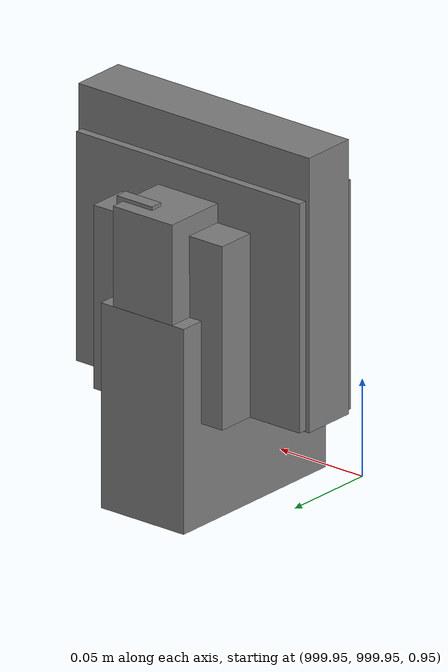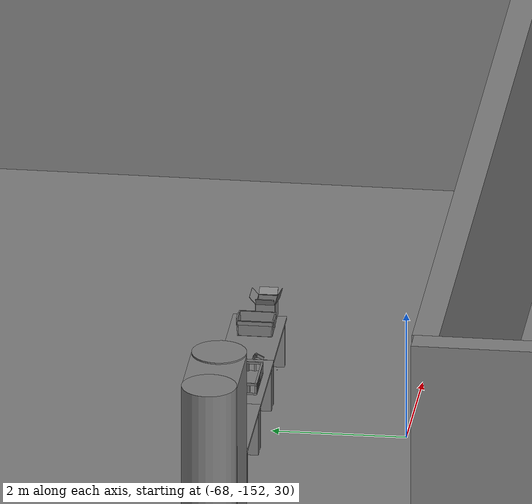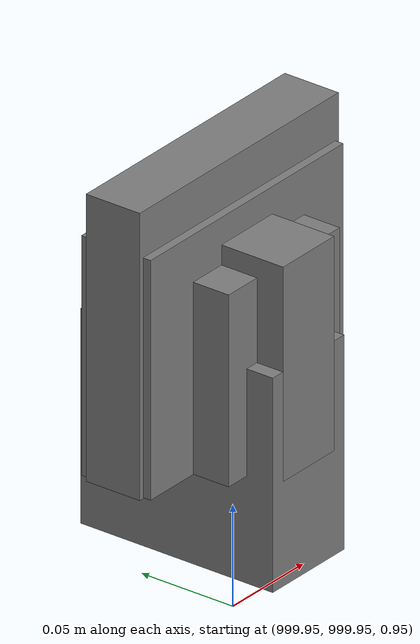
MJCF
<mujoco>
    <option gravity="0.000000000 0.000000000 -9.810000420" timestep="0.0049999999" integrator="implicitfast" density="1.225" viscosity="1.8000001e-05" noslip_iterations="10" iterations="100" sdf_iterations="50">
        <flag multiccd="disable"/>
    </option>
    <size memory="1000M"/>
    <compiler coordinate="local"/>
    <worldbody>
        <light cutoff="30" pos="0 1 1" dir="0 -1 -2"/>
        <light cutoff="30" pos="0 -1 1" dir="0 1 -2"/>
        <body pos="-64.866622925 -149.383972168 30.183746338" euler="89.999984741 89.999946594 0.000000000" name="openloong_gripper_2f85_fix_base_usda_bluebox_01">
            <geom contype="1" conaffinity="1" density="1000" type="box" material="" rgba="0.500000000 0.500000000 0.500000000 1.000000000" solimp="0.899999976 0.949999988 0.001000000" friction="1.000000000 0.005000000 0.000100000" solref="0.020000000 1.000000000" margin="0" condim="3" group="0" pos="0.276580811 0.187225342 0.000068665" quat="0.707106948 0.000077471 0.707106352 0.000077486" size="0.100000001 0.057999998 0.010000000" name="openloong_gripper_2f85_fix_base_usda_geom_312A0C9A_1A21_4701_A42A_B7FC9EA4CF25"/>
            <geom contype="1" conaffinity="1" density="1000" type="box" material="" rgba="0.500000000 0.500000000 0.500000000 1.000000000" solimp="0.899999976 0.949999988 0.001000000" friction="1.000000000 0.005000000 0.000100000" solref="0.020000000 1.000000000" margin="0" condim="3" group="0" pos="0.000000000 0.002883911 0.000000000" quat="0.999999881 0.000000000 0.000000000 0.000000000" size="0.254000008 0.003000000 0.172000006" name="openloong_gripper_2f85_fix_base_usda_geom_8E5F831E_B327_4328_82C4_96A20B275F59"/>
            <geom contype="1" conaffinity="1" density="1000" type="box" material="" rgba="0.500000000 0.500000000 0.500000000 1.000000000" solimp="0.899999976 0.949999988 0.001000000" friction="1.000000000 0.005000000 0.000100000" solref="0.020000000 1.000000000" margin="0" condim="3" group="0" pos="0.000000000 0.124874115 0.173484802" quat="0.999796331 0.020176515 -0.000000015 0.000000030" size="0.259999990 0.119999997 0.007000000" name="openloong_gripper_2f85_fix_base_usda_geom_C6CC64E9_3BEF_40A2_8212_279B4687A3A7"/>
            <geom contype="1" conaffinity="1" density="1000" type="box" material="" rgba="0.500000000 0.500000000 0.500000000 1.000000000" solimp="0.899999976 0.949999988 0.001000000" friction="1.000000000 0.005000000 0.000100000" solref="0.020000000 1.000000000" margin="0" condim="3" group="0" pos="0.000000000 0.124874115 -0.173469543" quat="0.999796331 -0.020176545 -0.000000015 0.000000000" size="0.259999990 0.119999997 0.007000000" name="openloong_gripper_2f85_fix_base_usda_geom_38498E37_72AB_4E18_A623_B405D1F510B8"/>
            <geom contype="1" conaffinity="1" density="1000" type="box" material="" rgba="0.500000000 0.500000000 0.500000000 1.000000000" solimp="0.899999976 0.949999988 0.001000000" friction="1.000000000 0.005000000 0.000100000" solref="0.020000000 1.000000000" margin="0" condim="3" group="0" pos="0.000000000 0.214008331 0.188980103" quat="0.999912977 0.013176724 0.000000015 0.000000000" size="0.259999990 0.029999999 0.012500000" name="openloong_gripper_2f85_fix_base_usda_geom_17095DB1_5B14_4FC2_848E_0E5A400F3833"/>
            <geom contype="1" conaffinity="1" density="1000" type="box" material="" rgba="0.500000000 0.500000000 0.500000000 1.000000000" solimp="0.899999976 0.949999988 0.001000000" friction="1.000000000 0.005000000 0.000100000" solref="0.020000000 1.000000000" margin="0" condim="3" group="0" pos="-0.258361816 0.125289917 0.001876831" quat="0.702796936 -0.020792112 0.710783124 0.020769298" size="0.189999998 0.119999997 0.009000000" name="openloong_gripper_2f85_fix_base_usda_geom_E9249655_DC4A_479B_B216_3A3907F8CF37"/>
            <geom contype="1" conaffinity="1" density="1000" type="box" material="" rgba="0.500000000 0.500000000 0.500000000 1.000000000" solimp="0.899999976 0.949999988 0.001000000" friction="1.000000000 0.005000000 0.000100000" solref="0.020000000 1.000000000" margin="0" condim="3" group="0" pos="0.000000000 0.214008331 -0.188980103" quat="0.999912977 -0.013176769 0.000000030 0.000000015" size="0.259999990 0.029999999 0.012500000" name="openloong_gripper_2f85_fix_base_usda_geom_5B113444_1B2A_42DD_8E09_5CACBF262FED"/>
            <geom contype="1" conaffinity="1" density="1000" type="box" material="" rgba="0.500000000 0.500000000 0.500000000 1.000000000" solimp="0.899999976 0.949999988 0.001000000" friction="1.000000000 0.005000000 0.000100000" solref="0.020000000 1.000000000" margin="0" condim="3" group="0" pos="-0.276611328 0.187225342 0.000068665" quat="0.707106650 0.000077441 0.707106709 0.000077456" size="0.100000001 0.057999998 0.010000000" name="openloong_gripper_2f85_fix_base_usda_geom_E093F499_989F_42A7_8B5B_C6AAD783FF9D"/>
            <geom contype="1" conaffinity="1" density="1000" type="box" material="" rgba="0.500000000 0.500000000 0.500000000 1.000000000" solimp="0.899999976 0.949999988 0.001000000" friction="1.000000000 0.005000000 0.000100000" solref="0.020000000 1.000000000" margin="0" condim="3" group="0" pos="0.258331299 0.125289917 0.001876831" quat="0.702851415 0.018856421 0.710823774 -0.019329369" size="0.189999998 0.119999997 0.009000000" name="openloong_gripper_2f85_fix_base_usda_geom_7DF5C8B3_FA39_4538_8E1E_64A1189044EE"/>
            <freejoint name="openloong_gripper_2f85_fix_base_usda_bluebox_01_joint"/>
            <site size="0.005000000 0.005000000 0.005000000" rgba="0.500000000 0.500000000 0.500000000 1.000000000" pos="0.000000000 0.000000000 0.000000000" quat="0.999961913 0.008726534 0.000000000 0.000000000" group="0" type="sphere" name="openloong_gripper_2f85_fix_base_usda_bluebox_01site"/>
        </body>
        <body pos="-64.496299744 -149.491867065 30.235729218" euler="0.000000000 0.000000000 89.999946594" name="openloong_gripper_2f85_fix_base_usda_cardboardbox_01">
            <geom contype="1" conaffinity="1" density="1000" type="box" material="" rgba="0.500000000 0.500000000 0.500000000 1.000000000" solimp="0.899999976 0.949999988 0.001000000" friction="1.000000000 0.005000000 0.000100000" solref="0.020000000 1.000000000" margin="0" condim="3" group="0" pos="-0.003166199 -0.004086494 0.005052090" quat="1.000000000 0.000000000 0.000000000 0.000000000" size="0.142499998 0.177500010 0.005000000" name="openloong_gripper_2f85_fix_base_usda_geom_FB9E6856_435C_4018_B11F_52B2F51CBA94"/>
            <geom contype="1" conaffinity="1" density="1000" type="box" material="" rgba="0.500000000 0.500000000 0.500000000 1.000000000" solimp="0.899999976 0.949999988 0.001000000" friction="1.000000000 0.005000000 0.000100000" solref="0.020000000 1.000000000" margin="0" condim="3" group="0" pos="-0.003166199 0.170316696 0.150570869" quat="1.000000000 0.000000000 0.000000000 0.000000000" size="0.142499998 0.005000000 0.149999991" name="openloong_gripper_2f85_fix_base_usda_geom_459DA7C0_19E7_41E8_8543_112E2FBE159F"/>
            <geom contype="1" conaffinity="1" density="1000" type="box" material="" rgba="0.500000000 0.500000000 0.500000000 1.000000000" solimp="0.899999976 0.949999988 0.001000000" friction="1.000000000 0.005000000 0.000100000" solref="0.020000000 1.000000000" margin="0" condim="3" group="0" pos="-0.147399902 -0.005307198 0.150570869" quat="1.000000000 0.000000000 0.000000000 0.000000000" size="0.005000000 0.177500010 0.149999991" name="openloong_gripper_2f85_fix_base_usda_geom_9A434856_A06F_45AD_97BE_42BCBD36A865"/>
            <geom contype="1" conaffinity="1" density="1000" type="box" material="" rgba="0.500000000 0.500000000 0.500000000 1.000000000" solimp="0.899999976 0.949999988 0.001000000" friction="1.000000000 0.005000000 0.000100000" solref="0.020000000 1.000000000" margin="0" condim="3" group="0" pos="0.140275955 -0.005307198 0.150570869" quat="1.000000000 0.000000000 0.000000000 0.000000000" size="0.005000000 0.177500010 0.149999991" name="openloong_gripper_2f85_fix_base_usda_geom_989E0E16_87E6_4F35_B0C4_973A8E8028CD"/>
            <geom contype="1" conaffinity="1" density="1000" type="box" material="" rgba="0.500000000 0.500000000 0.500000000 1.000000000" solimp="0.899999976 0.949999988 0.001000000" friction="1.000000000 0.005000000 0.000100000" solref="0.020000000 1.000000000" margin="0" condim="3" group="0" pos="-0.003166199 -0.181550980 0.150570869" quat="1.000000000 0.000000000 0.000000000 0.000000000" size="0.142499998 0.005000000 0.149999991" name="openloong_gripper_2f85_fix_base_usda_geom_9E2D26FD_1099_4EE0_8D49_D8157C230860"/>
            <freejoint name="openloong_gripper_2f85_fix_base_usda_cardboardbox_01_joint"/>
            <site size="0.005000000 0.005000000 0.005000000" rgba="0.500000000 0.500000000 0.500000000 1.000000000" pos="0.000000000 0.000000000 0.000000000" quat="0.999961913 0.008726535 0.000000000 0.000000000" group="0" type="sphere" name="openloong_gripper_2f85_fix_base_usda_site_1F058FF7_7C17_4C09_BC8C_DB7CD3ACB176"/>
            <body pos="0.139160156 -0.004048347 0.301930904" euler="-179.999954224 49.383502960 179.999954224" name="openloong_gripper_2f85_fix_base_usda_A1_006">
                <geom contype="1" conaffinity="1" density="1000" type="box" material="" rgba="0.500000000 0.500000000 0.500000000 1.000000000" solimp="0.899999976 0.949999988 0.001000000" friction="1.000000000 0.005000000 0.000100000" solref="0.020000000 1.000000000" margin="0" condim="3" group="0" pos="-0.071587563 0.000009537 0.001745224" quat="0.999999881 0.000000000 0.000000000 0.000000000" size="0.071249999 0.179999992 0.002500000" name="openloong_gripper_2f85_fix_base_usda_geom_37007F90_F18A_4A02_8E70_4F23F871A6A3"/>
                <joint armature="0" stiffness="0.07" damping="0.0099999998" axis="0.000000 1.000000 0.000000" type="hinge" name="openloong_gripper_2f85_fix_base_usda_A1_006"/>
            </body>
            <body pos="-0.145902634 -0.004086494 0.301938057" euler="-180.000000000 -60.000011444 -180.000000000" name="openloong_gripper_2f85_fix_base_usda_A2_006">
                <geom contype="1" conaffinity="1" density="1000" type="box" material="" rgba="0.500000000 0.500000000 0.500000000 1.000000000" solimp="0.899999976 0.949999988 0.001000000" friction="1.000000000 0.005000000 0.000100000" solref="0.020000000 1.000000000" margin="0" condim="3" group="0" pos="0.071268082 0.000009537 0.002717972" quat="0.000002921 0.000000000 -0.000000030 0.999999881" size="0.071249999 0.179999992 0.002500000" name="openloong_gripper_2f85_fix_base_usda_geom_70937421_E62B_41DC_B5C7_C7D57D18CFAD"/>
                <joint armature="0" stiffness="0.07" damping="0.0099999998" axis="0.000000 1.000000 0.000000" type="hinge" name="openloong_gripper_2f85_fix_base_usda_A2_006"/>
            </body>
            <body pos="-0.003385544 0.175991058 0.301930904" euler="-125.858116150 -0.000004561 0.000002331" name="openloong_gripper_2f85_fix_base_usda_B2_006">
                <geom contype="1" conaffinity="1" density="1000" type="box" material="" rgba="0.500000000 0.500000000 0.500000000 1.000000000" solimp="0.899999976 0.949999988 0.001000000" friction="1.000000000 0.005000000 0.000100000" solref="0.020000000 1.000000000" margin="0" condim="3" group="0" pos="0.000009537 -0.070939064 -0.002470016" quat="0.999614120 0.027776197 -0.000000015 0.000000030" size="0.137500003 0.064999998 0.005000000" name="openloong_gripper_2f85_fix_base_usda_geom_B0EF5F92_AAEB_4928_89DA_ABC11B18C0DD"/>
                <joint armature="0" stiffness="0.07" damping="0.0099999998" axis="1.000000 0.000000 0.000000" type="hinge" name="openloong_gripper_2f85_fix_base_usda_B2_006"/>
            </body>
            <body pos="-0.003385544 -0.184140205 0.301938057" euler="147.805557251 0.000000000 0.000000000" name="openloong_gripper_2f85_fix_base_usda_B1_006">
                <geom contype="1" conaffinity="1" density="1000" type="box" material="" rgba="0.500000000 0.500000000 0.500000000 1.000000000" solimp="0.899999976 0.949999988 0.001000000" friction="1.000000000 0.005000000 0.000100000" solref="0.020000000 1.000000000" margin="0" condim="3" group="0" pos="-0.000028610 0.070202351 -0.002703667" quat="0.999614179 -0.027776167 0.000000000 0.000000000" size="0.137500003 0.064999998 0.005000000" name="openloong_gripper_2f85_fix_base_usda_geom_329FF7BE_073E_4B12_BE8A_5E529992BEE7"/>
                <joint armature="0" stiffness="0.07" damping="0.0099999998" axis="1.000000 0.000000 0.000000" type="hinge" name="openloong_gripper_2f85_fix_base_usda_B1_006"/>
            </body>
        </body>
        <body pos="-65.882858276 -149.481979370 30.229999542" euler="-64.487716675 0.000000000 0.000000000" name="openloong_gripper_2f85_fix_base_usda_Barcode">
            <geom contype="1" conaffinity="1" density="1000" type="box" material="" rgba="0.500000000 0.500000000 0.500000000 1.000000000" solimp="0.899999976 0.949999988 0.001000000" friction="1.000000000 0.005000000 0.000100000" solref="0.020000000 1.000000000" margin="0" condim="3" group="0" pos="0.000000000 0.013038635 0.001419067" quat="0.000000000 0.000000000 0.000000000 1.000000119" size="0.034000002 0.010000000 0.017999999" name="openloong_gripper_2f85_fix_base_usda_geom_499B3B6D_4AE6_44D6_9DED_FAEBC896063F"/>
            <geom contype="1" conaffinity="1" density="1000" type="box" material="" rgba="0.500000000 0.500000000 0.500000000 1.000000000" solimp="0.899999976 0.949999988 0.001000000" friction="1.000000000 0.005000000 0.000100000" solref="0.020000000 1.000000000" margin="0" condim="3" group="0" pos="0.000000000 -0.035301208 -0.007095337" quat="0.000000000 0.000000000 -0.043619365 0.999048233" size="0.028999999 0.010000000 0.020000000" name="openloong_gripper_2f85_fix_base_usda_geom_01E40500_A22B_4FC0_8B6B_CAE9D31B438A"/>
            <geom contype="1" conaffinity="1" density="1000" type="box" material="" rgba="0.500000000 0.500000000 0.500000000 1.000000000" solimp="0.899999976 0.949999988 0.001000000" friction="1.000000000 0.005000000 0.000100000" solref="0.020000000 1.000000000" margin="0" condim="3" group="0" pos="0.000000000 -0.043411255 -0.011749268" quat="0.922262907 0.386563420 0.000000000 0.000000000" size="0.026000001 0.010000000 0.020000000" name="openloong_gripper_2f85_fix_base_usda_geom_807B4342_81FE_4A39_9C1B_5F83BFBC05FC"/>
            <geom contype="1" conaffinity="1" density="1000" type="box" material="" rgba="0.500000000 0.500000000 0.500000000 1.000000000" solimp="0.899999976 0.949999988 0.001000000" friction="1.000000000 0.005000000 0.000100000" solref="0.020000000 1.000000000" margin="0" condim="3" group="0" pos="0.000000000 -0.016967773 -0.031860352" quat="0.000000000 0.000000000 0.000000000 1.000000119" size="0.008000000 0.010000000 0.013000000" name="openloong_gripper_2f85_fix_base_usda_geom_ABF8233E_678C_45D2_9AA7_E965E2363A52"/>
            <geom contype="1" conaffinity="1" density="1000" type="box" material="" rgba="0.500000000 0.500000000 0.500000000 1.000000000" solimp="0.899999976 0.949999988 0.001000000" friction="1.000000000 0.005000000 0.000100000" solref="0.020000000 1.000000000" margin="0" condim="3" group="0" pos="0.000000000 -0.001869202 0.000312805" quat="0.953716993 0.300705761 0.000000000 0.000000000" size="0.032000002 0.010000000 0.018999999" name="openloong_gripper_2f85_fix_base_usda_geom_B86A1F4B_4BCD_4C22_ABA8_5354F49A6E94"/>
            <geom contype="1" conaffinity="1" density="1000" type="box" material="" rgba="0.500000000 0.500000000 0.500000000 1.000000000" solimp="0.899999976 0.949999988 0.001000000" friction="1.000000000 0.005000000 0.000100000" solref="0.020000000 1.000000000" margin="0" condim="3" group="0" pos="0.000000000 -0.019531250 -0.003173828" quat="0.953716993 0.300705761 0.000000000 0.000000000" size="0.030999999 0.010000000 0.020000000" name="openloong_gripper_2f85_fix_base_usda_geom_26DB6890_96D5_407A_9182_4CE5FEF79B4E"/>
            <geom contype="1" conaffinity="1" density="1000" type="box" material="" rgba="0.500000000 0.500000000 0.500000000 1.000000000" solimp="0.899999976 0.949999988 0.001000000" friction="1.000000000 0.005000000 0.000100000" solref="0.020000000 1.000000000" margin="0" condim="3" group="0" pos="0.000000000 -0.035301208 -0.007095337" quat="0.953716993 0.300705761 0.000000000 0.000000000" size="0.028999999 0.010000000 0.020000000" name="openloong_gripper_2f85_fix_base_usda_geom_90DAEEB2_39A3_4FBA_8655_7F71E6462FDA"/>
            <geom contype="1" conaffinity="1" density="1000" type="box" material="" rgba="0.500000000 0.500000000 0.500000000 1.000000000" solimp="0.899999976 0.949999988 0.001000000" friction="1.000000000 0.005000000 0.000100000" solref="0.020000000 1.000000000" margin="0" condim="3" group="0" pos="0.000000000 -0.042617798 -0.071121216" quat="0.000000000 0.000000000 0.000000000 1.000000119" size="0.013000000 0.021000000 0.059999999" name="openloong_gripper_2f85_fix_base_usda_geom_6D599E06_E8CF_4AFF_835E_499CEAD2554E"/>
            <freejoint name="openloong_gripper_2f85_fix_base_usda_Barcode_joint"/>
            <site size="0.005000000 0.005000000 0.005000000" rgba="0.500000000 0.500000000 0.500000000 1.000000000" pos="0.000000000 0.000000000 0.000000000" quat="1.000000000 0.000000000 0.000000000 0.000000000" group="0" type="sphere" name="openloong_gripper_2f85_fix_base_usda_Barcode_site"/>
        </body>
        <body pos="-66.745018005 -149.392349243 30.184000015" euler="0.000000000 0.000000000 89.999946594" name="[22330030786009]_Basket_01">
            <geom contype="1" conaffinity="1" density="1000" type="box" material="" rgba="0.500000000 0.500000000 0.500000000 1.000000000" solimp="0.899999976 0.949999988 0.001000000" friction="1.000000000 0.005000000 0.000100000" solref="0.020000000 1.000000000" margin="0" condim="3" group="0" pos="-0.052425385 0.389207840 0.089787483" quat="0.707107008 0.000000000 0.000000000 0.707106411" size="0.014249999 0.014249999 0.059999999" name="[22330030786009]_geom_34D42A26_F888_47A4_8F58_C0741197C2B2"/>
            <geom contype="1" conaffinity="1" density="1000" type="box" material="" rgba="0.500000000 0.500000000 0.500000000 1.000000000" solimp="0.899999976 0.949999988 0.001000000" friction="1.000000000 0.005000000 0.000100000" solref="0.020000000 1.000000000" margin="0" condim="3" group="0" pos="0.264015198 -0.133043289 0.089787483" quat="0.707107008 0.000000000 0.000000000 0.707106411" size="0.014249999 0.014249999 0.059999999" name="[22330030786009]_geom_49A582B4_0BE6_4B74_A5D5_0DCB207FD8CB"/>
            <geom contype="1" conaffinity="1" density="1000" type="box" material="" rgba="0.500000000 0.500000000 0.500000000 1.000000000" solimp="0.899999976 0.949999988 0.001000000" friction="1.000000000 0.005000000 0.000100000" solref="0.020000000 1.000000000" margin="0" condim="3" group="0" pos="-0.264015198 -0.265548706 0.089793205" quat="0.707107008 0.000000000 0.000000000 0.707106411" size="0.014249999 0.014249999 0.059999999" name="[22330030786009]_geom_6B1C649A_F742_4561_9EA4_2F33CC0AD81D"/>
            <geom contype="1" conaffinity="1" density="1000" type="box" material="" rgba="0.500000000 0.500000000 0.500000000 1.000000000" solimp="0.899999976 0.949999988 0.001000000" friction="1.000000000 0.005000000 0.000100000" solref="0.020000000 1.000000000" margin="0" condim="3" group="0" pos="-0.160263062 -0.389322281 0.089793205" quat="0.707107008 0.000000000 0.000000000 0.707106411" size="0.014249999 0.014249999 0.059999999" name="[22330030786009]_geom_62CE7200_25A9_4829_9888_B419AA9525F6"/>
            <geom contype="1" conaffinity="1" density="1000" type="box" material="" rgba="0.500000000 0.500000000 0.500000000 1.000000000" solimp="0.899999976 0.949999988 0.001000000" friction="1.000000000 0.005000000 0.000100000" solref="0.020000000 1.000000000" margin="0" condim="3" group="0" pos="0.162265778 -0.389322281 0.089787483" quat="0.707107008 0.000000000 0.000000000 0.707106411" size="0.014249999 0.014249999 0.059999999" name="[22330030786009]_geom_19FF36D8_1FD6_4716_AA03_CBC656729C2F"/>
            <geom contype="1" conaffinity="1" density="1000" type="box" material="" rgba="0.500000000 0.500000000 0.500000000 1.000000000" solimp="0.899999976 0.949999988 0.001000000" friction="1.000000000 0.005000000 0.000100000" solref="0.020000000 1.000000000" margin="0" condim="3" group="0" pos="0.264015198 0.389207840 0.089787483" quat="0.707107008 0.000000000 0.000000000 0.707106411" size="0.014249999 0.014249999 0.059999999" name="[22330030786009]_geom_B2B2C999_47D3_4763_9995_434B3D1CB27D"/>
            <geom contype="1" conaffinity="1" density="1000" type="box" material="" rgba="0.500000000 0.500000000 0.500000000 1.000000000" solimp="0.899999976 0.949999988 0.001000000" friction="1.000000000 0.005000000 0.000100000" solref="0.020000000 1.000000000" margin="0" condim="3" group="0" pos="-0.264015198 -0.133043289 0.089793205" quat="0.707107008 0.000000000 0.000000000 0.707106411" size="0.014249999 0.014249999 0.059999999" name="[22330030786009]_geom_57E5DF3B_1837_4B67_B182_4015762A31A3"/>
            <geom contype="1" conaffinity="1" density="1000" type="box" material="" rgba="0.500000000 0.500000000 0.500000000 1.000000000" solimp="0.899999976 0.949999988 0.001000000" friction="1.000000000 0.005000000 0.000100000" solref="0.020000000 1.000000000" margin="0" condim="3" group="0" pos="-0.264026642 0.269256592 0.089793205" quat="0.707107008 0.000000000 0.000000000 0.707106411" size="0.014249999 0.014249999 0.059999999" name="[22330030786009]_geom_D2005167_A7FB_4394_99B8_497AF244591C"/>
            <geom contype="1" conaffinity="1" density="1000" type="box" material="" rgba="0.500000000 0.500000000 0.500000000 1.000000000" solimp="0.899999976 0.949999988 0.001000000" friction="1.000000000 0.005000000 0.000100000" solref="0.020000000 1.000000000" margin="0" condim="3" group="0" pos="0.054462433 0.389207840 0.089787483" quat="0.707107008 0.000000000 0.000000000 0.707106411" size="0.014249999 0.014249999 0.059999999" name="[22330030786009]_geom_AF7498C1_D969_419D_AA64_BD6FC71BCC05"/>
            <geom contype="1" conaffinity="1" density="1000" type="box" material="" rgba="0.500000000 0.500000000 0.500000000 1.000000000" solimp="0.899999976 0.949999988 0.001000000" friction="1.000000000 0.005000000 0.000100000" solref="0.020000000 1.000000000" margin="0" condim="3" group="0" pos="0.054462433 -0.389322281 0.089787483" quat="0.707107008 0.000000000 0.000000000 0.707106411" size="0.014249999 0.014249999 0.059999999" name="[22330030786009]_geom_844B6933_069D_418F_8723_FA0C364F57C8"/>
            <geom contype="1" conaffinity="1" density="1000" type="box" material="" rgba="0.500000000 0.500000000 0.500000000 1.000000000" solimp="0.899999976 0.949999988 0.001000000" friction="1.000000000 0.005000000 0.000100000" solref="0.020000000 1.000000000" margin="0" condim="3" group="0" pos="0.264015198 0.269256592 0.089793205" quat="0.707107008 0.000000000 0.000000000 0.707106411" size="0.014249999 0.014249999 0.059999999" name="[22330030786009]_geom_11E7E88A_E498_460F_8009_9282E5C9B80C"/>
            <geom contype="1" conaffinity="1" density="1000" type="box" material="" rgba="0.500000000 0.500000000 0.500000000 1.000000000" solimp="0.899999976 0.949999988 0.001000000" friction="1.000000000 0.005000000 0.000100000" solref="0.020000000 1.000000000" margin="0" condim="3" group="0" pos="0.264015198 -0.389322281 0.089787483" quat="0.707107008 0.000000000 0.000000000 0.707106411" size="0.014249999 0.014249999 0.059999999" name="[22330030786009]_geom_CB9E120A_CEE8_4763_91E1_8FED8F3EB52B"/>
            <geom contype="1" conaffinity="1" density="1000" type="box" material="" rgba="0.500000000 0.500000000 0.500000000 1.000000000" solimp="0.899999976 0.949999988 0.001000000" friction="1.000000000 0.005000000 0.000100000" solref="0.020000000 1.000000000" margin="0" condim="3" group="0" pos="0.000000000 0.000000000 0.015998840" quat="0.707107008 0.000000000 0.000000000 0.707106411" size="0.403499991 0.279000014 0.015750000" name="[22330030786009]_geom_1267AB2D_CA30_41BA_9BE6_76418BC766A5"/>
            <geom contype="1" conaffinity="1" density="1000" type="box" material="" rgba="0.500000000 0.500000000 0.500000000 1.000000000" solimp="0.899999976 0.949999988 0.001000000" friction="1.000000000 0.005000000 0.000100000" solref="0.020000000 1.000000000" margin="0" condim="3" group="0" pos="0.000000000 -0.389476776 0.163619041" quat="0.707107008 0.000000000 0.000000000 0.707106411" size="0.015000000 0.277500004 0.015750000" name="[22330030786009]_geom_C11F5D58_12FA_4063_AF74_5235363A2ADD"/>
            <geom contype="1" conaffinity="1" density="1000" type="box" material="" rgba="0.500000000 0.500000000 0.500000000 1.000000000" solimp="0.899999976 0.949999988 0.001000000" friction="1.000000000 0.005000000 0.000100000" solref="0.020000000 1.000000000" margin="0" condim="3" group="0" pos="0.162265778 0.389207840 0.089787483" quat="0.707107008 0.000000000 0.000000000 0.707106411" size="0.014249999 0.014249999 0.059999999" name="[22330030786009]_geom_07B63D55_906A_44A9_A035_68FA3641186D"/>
            <geom contype="1" conaffinity="1" density="1000" type="box" material="" rgba="0.500000000 0.500000000 0.500000000 1.000000000" solimp="0.899999976 0.949999988 0.001000000" friction="1.000000000 0.005000000 0.000100000" solref="0.020000000 1.000000000" margin="0" condim="3" group="0" pos="0.000000000 0.389471054 0.163619041" quat="0.707107008 0.000000000 0.000000000 0.707106411" size="0.015000000 0.277500004 0.015750000" name="[22330030786009]_geom_164EADA2_18A2_4F95_A0C9_910759A1AB79"/>
            <geom contype="1" conaffinity="1" density="1000" type="box" material="" rgba="0.500000000 0.500000000 0.500000000 1.000000000" solimp="0.899999976 0.949999988 0.001000000" friction="1.000000000 0.005000000 0.000100000" solref="0.020000000 1.000000000" margin="0" condim="3" group="0" pos="-0.263511658 0.000000000 0.163619041" quat="0.707107008 0.000000000 0.000000000 0.707106411" size="0.403499991 0.015000000 0.015750000" name="[22330030786009]_geom_FDB2E24B_3B9D_4E1B_AA91_33003378B01C"/>
            <geom contype="1" conaffinity="1" density="1000" type="box" material="" rgba="0.500000000 0.500000000 0.500000000 1.000000000" solimp="0.899999976 0.949999988 0.001000000" friction="1.000000000 0.005000000 0.000100000" solref="0.020000000 1.000000000" margin="0" condim="3" group="0" pos="-0.264015198 0.141334534 0.089793205" quat="0.707107008 0.000000000 0.000000000 0.707106411" size="0.014249999 0.014249999 0.059999999" name="[22330030786009]_geom_201DF11F_AB70_434D_8571_BBBB709414E2"/>
            <geom contype="1" conaffinity="1" density="1000" type="box" material="" rgba="0.500000000 0.500000000 0.500000000 1.000000000" solimp="0.899999976 0.949999988 0.001000000" friction="1.000000000 0.005000000 0.000100000" solref="0.020000000 1.000000000" margin="0" condim="3" group="0" pos="0.264015198 -0.265548706 0.089787483" quat="0.707107008 0.000000000 0.000000000 0.707106411" size="0.014249999 0.014249999 0.059999999" name="[22330030786009]_geom_DDEF856D_C083_45FA_8005_534DC645CC5F"/>
            <geom contype="1" conaffinity="1" density="1000" type="box" material="" rgba="0.500000000 0.500000000 0.500000000 1.000000000" solimp="0.899999976 0.949999988 0.001000000" friction="1.000000000 0.005000000 0.000100000" solref="0.020000000 1.000000000" margin="0" condim="3" group="0" pos="-0.160263062 0.389207840 0.089787483" quat="0.707107008 0.000000000 0.000000000 0.707106411" size="0.014249999 0.014249999 0.059999999" name="[22330030786009]_geom_EF450C70_0D82_46D6_95B3_615AE552E903"/>
            <geom contype="1" conaffinity="1" density="1000" type="box" material="" rgba="0.500000000 0.500000000 0.500000000 1.000000000" solimp="0.899999976 0.949999988 0.001000000" friction="1.000000000 0.005000000 0.000100000" solref="0.020000000 1.000000000" margin="0" condim="3" group="0" pos="-0.052425385 -0.389322281 0.089787483" quat="0.707107008 0.000000000 0.000000000 0.707106411" size="0.014249999 0.014249999 0.059999999" name="[22330030786009]_geom_2D12305A_9648_49B1_991C_39E177513CFF"/>
            <geom contype="1" conaffinity="1" density="1000" type="box" material="" rgba="0.500000000 0.500000000 0.500000000 1.000000000" solimp="0.899999976 0.949999988 0.001000000" friction="1.000000000 0.005000000 0.000100000" solref="0.020000000 1.000000000" margin="0" condim="3" group="0" pos="-0.264026642 -0.389322281 0.089793205" quat="0.707107008 0.000000000 0.000000000 0.707106411" size="0.014249999 0.014249999 0.059999999" name="[22330030786009]_geom_28726170_EE12_49CD_8FAD_71655DA6951A"/>
            <geom contype="1" conaffinity="1" density="1000" type="box" material="" rgba="0.500000000 0.500000000 0.500000000 1.000000000" solimp="0.899999976 0.949999988 0.001000000" friction="1.000000000 0.005000000 0.000100000" solref="0.020000000 1.000000000" margin="0" condim="3" group="0" pos="0.264015198 0.141334534 0.089787483" quat="0.707107008 0.000000000 0.000000000 0.707106411" size="0.014249999 0.014249999 0.059999999" name="[22330030786009]_geom_6A1CE7BA_FB22_4C35_8F78_EFD485B046A0"/>
            <geom contype="1" conaffinity="1" density="1000" type="box" material="" rgba="0.500000000 0.500000000 0.500000000 1.000000000" solimp="0.899999976 0.949999988 0.001000000" friction="1.000000000 0.005000000 0.000100000" solref="0.020000000 1.000000000" margin="0" condim="3" group="0" pos="-0.264015198 0.389207840 0.089793205" quat="0.707107008 0.000000000 0.000000000 0.707106411" size="0.014249999 0.014249999 0.059999999" name="[22330030786009]_geom_191ECFCA_ABAA_422B_84CA_4283AB7D94CD"/>
            <geom contype="1" conaffinity="1" density="1000" type="box" material="" rgba="0.500000000 0.500000000 0.500000000 1.000000000" solimp="0.899999976 0.949999988 0.001000000" friction="1.000000000 0.005000000 0.000100000" solref="0.020000000 1.000000000" margin="0" condim="3" group="0" pos="0.264015198 0.004480362 0.089787483" quat="0.707107008 0.000000000 0.000000000 0.707106411" size="0.014249999 0.014249999 0.059999999" name="[22330030786009]_geom_1B73E4B9_54C5_40F9_9678_C03CCF76D30F"/>
            <geom contype="1" conaffinity="1" density="1000" type="box" material="" rgba="0.500000000 0.500000000 0.500000000 1.000000000" solimp="0.899999976 0.949999988 0.001000000" friction="1.000000000 0.005000000 0.000100000" solref="0.020000000 1.000000000" margin="0" condim="3" group="0" pos="0.263694763 -0.000011444 0.163619041" quat="0.707107008 0.000000000 0.000000000 0.707106411" size="0.403499991 0.015000000 0.015750000" name="[22330030786009]_geom_57A5A8E0_B6A9_41D2_B2D2_4AD0C13DF546"/>
            <geom contype="1" conaffinity="1" density="1000" type="box" material="" rgba="0.500000000 0.500000000 0.500000000 1.000000000" solimp="0.899999976 0.949999988 0.001000000" friction="1.000000000 0.005000000 0.000100000" solref="0.020000000 1.000000000" margin="0" condim="3" group="0" pos="-0.264015198 0.004480362 0.089793205" quat="0.707107008 0.000000000 0.000000000 0.707106411" size="0.014249999 0.014249999 0.059999999" name="[22330030786009]_geom_A4B64931_EF36_4E00_90EE_22179619262E"/>
            <freejoint name="[22330030786009]_joint_1FA660A1_4A72_4EDF_91EE_ECAECFF6AF58"/>
        </body>
        <body pos="0.000000000 0.000000000 0.000000000" euler="0.000000000 0.000000000 0.000000000" name="Static Objects_Static Objects">
            <geom contype="1" conaffinity="1" density="1000" type="box" material="" rgba="0.500000000 0.500000000 0.500000000 1.000000000" solimp="0.899999976 0.949999988 0.001000000" friction="1.000000000 0.005000000 0.000100000" solref="0.020000000 1.000000000" margin="0" condim="3" group="0" pos="-67.544113159 -149.365814209 29.727830887" quat="0.500000417 0.499999970 0.499999553 0.499999970" size="0.381000012 0.319999993 0.041000001" name="Static Objects_geom_51D82326_F97E_45A1_AEFA_348F90237B98"/>
            <geom contype="1" conaffinity="1" density="1000" type="box" material="" rgba="0.500000000 0.500000000 0.500000000 1.000000000" solimp="0.899999976 0.949999988 0.001000000" friction="1.000000000 0.005000000 0.000100000" solref="0.020000000 1.000000000" margin="0" condim="3" group="0" pos="-68.239501953 -149.365814209 30.086868286" quat="0.500000417 0.499999970 0.499999553 0.499999970" size="0.370999992 0.039500002 0.745000005" name="Static Objects_geom_C5807312_C552_4C62_98D9_00D4FC67A2FF"/>
            <geom contype="1" conaffinity="1" density="1000" type="box" material="" rgba="0.500000000 0.500000000 0.500000000 1.000000000" solimp="0.899999976 0.949999988 0.001000000" friction="1.000000000 0.005000000 0.000100000" solref="0.020000000 1.000000000" margin="0" condim="3" group="0" pos="-68.239501953 -149.365814209 30.147235870" quat="0.500000417 0.499999970 0.499999553 0.499999970" size="0.400000006 0.022000000 0.800000012" name="Static Objects_geom_ACC2239D_C0FF_4521_8162_93C8C5929B7A"/>
            <geom contype="1" conaffinity="1" density="1000" type="box" material="" rgba="0.500000000 0.500000000 0.500000000 1.000000000" solimp="0.899999976 0.949999988 0.001000000" friction="1.000000000 0.005000000 0.000100000" solref="0.020000000 1.000000000" margin="0" condim="3" group="0" pos="-68.934890747 -149.365814209 29.727830887" quat="0.500000417 0.499999970 0.499999553 0.499999970" size="0.381000012 0.319999993 0.041000001" name="Static Objects_geom_1D82D452_107C_415D_AAC7_8F1BC6BFBC89"/>
            <geom contype="1" conaffinity="1" density="1000" type="box" material="" rgba="0.500000000 0.500000000 0.500000000 1.000000000" solimp="0.899999976 0.949999988 0.001000000" friction="1.000000000 0.005000000 0.000100000" solref="0.020000000 1.000000000" margin="0" condim="3" group="0" pos="-68.239501953 -149.365814209 29.561563492" quat="0.500000417 0.499999970 0.499999553 0.499999970" size="0.020000000 0.022000000 0.660000026" name="Static Objects_geom_E82898F4_BA61_4AAA_92AB_E32864E75B61"/>
            <geom contype="1" conaffinity="1" density="1000" type="box" material="" rgba="0.500000000 0.500000000 0.500000000 1.000000000" solimp="0.899999976 0.949999988 0.001000000" friction="1.000000000 0.005000000 0.000100000" solref="0.020000000 1.000000000" margin="0" condim="3" group="0" pos="-65.945671082 -149.365814209 29.727830887" quat="0.500000417 0.499999970 0.499999553 0.499999970" size="0.381000012 0.319999993 0.041000001" name="Static Objects_geom_A385BD8F_02CB_402C_9BFC_B32EC8366960"/>
            <geom contype="1" conaffinity="1" density="1000" type="box" material="" rgba="0.500000000 0.500000000 0.500000000 1.000000000" solimp="0.899999976 0.949999988 0.001000000" friction="1.000000000 0.005000000 0.000100000" solref="0.020000000 1.000000000" margin="0" condim="3" group="0" pos="-66.641059875 -149.365814209 30.086868286" quat="0.500000417 0.499999970 0.499999553 0.499999970" size="0.370999992 0.039500002 0.745000005" name="Static Objects_geom_625E52BA_39FA_4646_A9CC_18E6973446B4"/>
            <geom contype="1" conaffinity="1" density="1000" type="box" material="" rgba="0.500000000 0.500000000 0.500000000 1.000000000" solimp="0.899999976 0.949999988 0.001000000" friction="1.000000000 0.005000000 0.000100000" solref="0.020000000 1.000000000" margin="0" condim="3" group="0" pos="-66.641059875 -149.365814209 30.147235870" quat="0.500000417 0.499999970 0.499999553 0.499999970" size="0.400000006 0.022000000 0.800000012" name="Static Objects_geom_D12BC26C_9BC4_4AFB_92D0_5A75C395F207"/>
            <geom contype="1" conaffinity="1" density="1000" type="box" material="" rgba="0.500000000 0.500000000 0.500000000 1.000000000" solimp="0.899999976 0.949999988 0.001000000" friction="1.000000000 0.005000000 0.000100000" solref="0.020000000 1.000000000" margin="0" condim="3" group="0" pos="-67.336448669 -149.365814209 29.727830887" quat="0.500000417 0.499999970 0.499999553 0.499999970" size="0.381000012 0.319999993 0.041000001" name="Static Objects_geom_5911F2B4_C98E_4D2E_8387_601B520981ED"/>
            <geom contype="1" conaffinity="1" density="1000" type="box" material="" rgba="0.500000000 0.500000000 0.500000000 1.000000000" solimp="0.899999976 0.949999988 0.001000000" friction="1.000000000 0.005000000 0.000100000" solref="0.020000000 1.000000000" margin="0" condim="3" group="0" pos="-66.641059875 -149.365814209 29.561563492" quat="0.500000417 0.499999970 0.499999553 0.499999970" size="0.020000000 0.022000000 0.660000026" name="Static Objects_geom_E3A71BD1_EE89_49FC_90DF_EC6B44A979DB"/>
            <geom contype="1" conaffinity="1" density="1000" type="box" material="" rgba="0.500000000 0.500000000 0.500000000 1.000000000" solimp="0.899999976 0.949999988 0.001000000" friction="1.000000000 0.005000000 0.000100000" solref="0.020000000 1.000000000" margin="0" condim="3" group="0" pos="-64.338577271 -149.365814209 29.727830887" quat="0.500000417 0.499999970 0.499999553 0.499999970" size="0.381000012 0.319999993 0.041000001" name="Static Objects_geom_BA09CE45_FB2A_43F2_9FCD_96BF6BF9368C"/>
            <geom contype="1" conaffinity="1" density="1000" type="box" material="" rgba="0.500000000 0.500000000 0.500000000 1.000000000" solimp="0.899999976 0.949999988 0.001000000" friction="1.000000000 0.005000000 0.000100000" solref="0.020000000 1.000000000" margin="0" condim="3" group="0" pos="-65.033966064 -149.365814209 30.086868286" quat="0.500000417 0.499999970 0.499999553 0.499999970" size="0.370999992 0.039500002 0.745000005" name="Static Objects_geom_78B7CBBD_8925_4264_BA11_98164F3A5EC6"/>
            <geom contype="1" conaffinity="1" density="1000" type="box" material="" rgba="0.500000000 0.500000000 0.500000000 1.000000000" solimp="0.899999976 0.949999988 0.001000000" friction="1.000000000 0.005000000 0.000100000" solref="0.020000000 1.000000000" margin="0" condim="3" group="0" pos="-65.033966064 -149.365814209 30.147235870" quat="0.500000417 0.499999970 0.499999553 0.499999970" size="0.400000006 0.022000000 0.800000012" name="Static Objects_geom_4401F35B_6347_45F4_9CFD_ED89B93A130C"/>
            <geom contype="1" conaffinity="1" density="1000" type="box" material="" rgba="0.500000000 0.500000000 0.500000000 1.000000000" solimp="0.899999976 0.949999988 0.001000000" friction="1.000000000 0.005000000 0.000100000" solref="0.020000000 1.000000000" margin="0" condim="3" group="0" pos="-65.729354858 -149.365814209 29.727830887" quat="0.500000417 0.499999970 0.499999553 0.499999970" size="0.381000012 0.319999993 0.041000001" name="Static Objects_geom_D2ED2F6F_6C9F_49FB_BABA_C09890D2B91A"/>
            <geom contype="1" conaffinity="1" density="1000" type="box" material="" rgba="0.500000000 0.500000000 0.500000000 1.000000000" solimp="0.899999976 0.949999988 0.001000000" friction="1.000000000 0.005000000 0.000100000" solref="0.020000000 1.000000000" margin="0" condim="3" group="0" pos="-65.033966064 -149.365814209 29.561563492" quat="0.500000417 0.499999970 0.499999553 0.499999970" size="0.020000000 0.022000000 0.660000026" name="Static Objects_geom_288B112A_DC3F_4949_A5F9_498DA1A9E4B9"/>
            <geom contype="1" conaffinity="1" density="1000" type="box" material="" rgba="0.500000000 0.500000000 0.500000000 1.000000000" solimp="0.899999976 0.949999988 0.001000000" friction="1.000000000 0.005000000 0.000100000" solref="0.020000000 1.000000000" margin="0" condim="3" group="0" pos="-61.754566193 -137.853729248 33.906845093" quat="0.707107067 0.000000000 0.000000000 0.707106471" size="0.759999990 0.759999990 4.500000000" name="Static Objects_geom_28AA74B8_CB36_481F_9F1E_BBF8B7DB1212"/>
            <geom contype="1" conaffinity="1" density="1000" type="box" material="" rgba="0.500000000 0.500000000 0.500000000 1.000000000" solimp="0.899999976 0.949999988 0.001000000" friction="1.000000000 0.005000000 0.000100000" solref="0.020000000 1.000000000" margin="0" condim="3" group="0" pos="-57.511135101 -144.927108765 31.707921982" quat="1.000000000 0.000000000 0.000000000 0.000000000" size="0.200000003 8.000000000 2.299999952" name="Static Objects_geom_6C40AB84_B985_4684_8A9B_4A0F0AEC4E1C"/>
            <geom contype="1" conaffinity="1" density="1000" type="box" material="" rgba="0.500000000 0.500000000 0.500000000 1.000000000" solimp="0.899999976 0.949999988 0.001000000" friction="1.000000000 0.005000000 0.000100000" solref="0.020000000 1.000000000" margin="0" condim="3" group="0" pos="-80.517646790 -157.574050903 31.688196182" quat="0.707107067 0.000000000 0.000000000 0.707106471" size="0.600000024 0.600000024 2.299999952" name="Static Objects_geom_B9B52F22_47E3_4C06_A275_CF083645BBD9"/>
            <geom contype="1" conaffinity="1" density="1000" type="box" material="" rgba="0.500000000 0.500000000 0.500000000 1.000000000" solimp="0.899999976 0.949999988 0.001000000" friction="1.000000000 0.005000000 0.000100000" solref="0.020000000 1.000000000" margin="0" condim="3" group="0" pos="-80.711044312 -147.414932251 31.666158676" quat="1.000000000 0.000000000 0.000000000 0.000000000" size="0.200000003 10.000000000 2.299999952" name="Static Objects_geom_3621F2BD_D859_43F7_9819_A9826A54ADC2"/>
            <geom contype="1" conaffinity="1" density="1000" type="box" material="" rgba="0.500000000 0.500000000 0.500000000 1.000000000" solimp="0.899999976 0.949999988 0.001000000" friction="1.000000000 0.005000000 0.000100000" solref="0.020000000 1.000000000" margin="0" condim="3" group="0" pos="-57.687217712 -137.434692383 31.688196182" quat="0.707107067 0.000000000 0.000000000 0.707106471" size="0.600000024 0.600000024 2.299999952" name="Static Objects_geom_09A034D3_94AF_45A7_9952_D96C2446B941"/>
            <geom contype="1" conaffinity="1" density="1000" type="box" material="" rgba="0.500000000 0.500000000 0.500000000 1.000000000" solimp="0.899999976 0.949999988 0.001000000" friction="1.000000000 0.005000000 0.000100000" solref="0.020000000 1.000000000" margin="0" condim="3" group="0" pos="-69.537033081 -140.263229370 31.714921951" quat="0.707107067 0.000000000 0.000000000 0.707106471" size="0.759999990 4.500000000 2.299999952" name="Static Objects_geom_5CC18873_761E_44AE_B437_52436A426159"/>
            <geom contype="1" conaffinity="1" density="1000" type="box" material="" rgba="0.500000000 0.500000000 0.500000000 1.000000000" solimp="0.899999976 0.949999988 0.001000000" friction="1.000000000 0.005000000 0.000100000" solref="0.020000000 1.000000000" margin="0" condim="3" group="0" pos="-80.073638916 -137.853713989 33.906845093" quat="0.707107067 0.000000000 0.000000000 0.707106471" size="0.759999990 0.759999990 4.500000000" name="Static Objects_geom_47148E21_7ACD_4CB4_83FC_14010BA8599F"/>
            <geom contype="1" conaffinity="1" density="1000" type="box" material="" rgba="0.500000000 0.500000000 0.500000000 1.000000000" solimp="0.899999976 0.949999988 0.001000000" friction="1.000000000 0.005000000 0.000100000" solref="0.020000000 1.000000000" margin="0" condim="3" group="0" pos="-73.406707764 -155.734664917 31.707921982" quat="1.000000000 0.000000000 0.000000000 0.000000000" size="0.200000003 3.000000000 2.299999952" name="Static Objects_geom_32632D2F_966F_4141_9A83_42ED309D6822"/>
            <geom contype="1" conaffinity="1" density="1000" type="box" material="" rgba="0.500000000 0.500000000 0.500000000 1.000000000" solimp="0.899999976 0.949999988 0.001000000" friction="1.000000000 0.005000000 0.000100000" solref="0.020000000 1.000000000" margin="0" condim="3" group="0" pos="-68.497543335 -137.448257446 31.707921982" quat="0.707107067 0.000000000 0.000000000 0.707106471" size="0.200000003 14.000000000 2.299999952" name="Static Objects_geom_669651A3_1780_4738_8A74_8DC96B058F68"/>
            <geom contype="1" conaffinity="1" density="1000" type="cylinder" material="" rgba="0.500000000 0.500000000 0.500000000 1.000000000" solimp="0.899999976 0.949999988 0.001000000" friction="1.000000000 0.005000000 0.000100000" solref="0.020000000 1.000000000" margin="0" condim="3" group="0" pos="-68.868522644 -142.134506226 31.711090088" quat="0.707107067 0.000000000 0.000000000 0.707106471" size="0.509999990 2.299999952 1.000000000" name="Static Objects_geom_CDEEDDF2_63E3_4DFB_87E2_0D318F0EF318"/>
            <geom contype="1" conaffinity="1" density="1000" type="plane" material="" rgba="0.500000000 0.500000000 0.500000000 1.000000000" solimp="0.899999976 0.949999988 0.001000000" friction="1.000000000 0.005000000 0.000100000" solref="0.020000000 1.000000000" margin="0" condim="3" group="0" pos="-72.873703003 -147.131927490 29.409669876" quat="1.000000000 0.000000000 0.000000000 0.000000000" size="18.000000000 14.000000000 1.000000000" name="Static Objects_geom_54009D12_F227_4289_BC2A_D6F163926561"/>
            <geom contype="1" conaffinity="1" density="1000" type="box" material="" rgba="0.500000000 0.500000000 0.500000000 1.000000000" solimp="0.899999976 0.949999988 0.001000000" friction="1.000000000 0.005000000 0.000100000" solref="0.020000000 1.000000000" margin="0" condim="3" group="0" pos="-79.943580627 -157.782272339 31.707921982" quat="0.707107067 0.000000000 0.000000000 0.707106471" size="0.200000003 7.000000000 2.299999952" name="Static Objects_geom_B9A02333_3C99_4AF7_8BCC_EE3EE0BD6153"/>
            <geom contype="1" conaffinity="1" density="1000" type="box" material="" rgba="0.500000000 0.500000000 0.500000000 1.000000000" solimp="0.899999976 0.949999988 0.001000000" friction="1.000000000 0.005000000 0.000100000" solref="0.020000000 1.000000000" margin="0" condim="3" group="0" pos="-65.421028137 -152.903442383 31.707921982" quat="0.707107067 0.000000000 0.000000000 0.707106471" size="0.200000003 7.800000191 2.299999952" name="Static Objects_geom_C707E535_97B8_452C_BDFF_0765BC1E4E6F"/>
            <geom contype="1" conaffinity="1" density="1000" type="box" material="" rgba="0.500000000 0.500000000 0.500000000 1.000000000" solimp="0.899999976 0.949999988 0.001000000" friction="1.000000000 0.005000000 0.000100000" solref="0.020000000 1.000000000" margin="0" condim="3" group="0" pos="-74.776908875 -149.964416504 31.688196182" quat="1.000000000 0.000000000 0.000000000 0.000000000" size="0.600000024 0.409999996 2.299999952" name="Static Objects_geom_A465FF40_506B_4E37_889A_22DFBAA2A237"/>
            <geom contype="1" conaffinity="1" density="1000" type="cylinder" material="" rgba="0.500000000 0.500000000 0.500000000 1.000000000" solimp="0.899999976 0.949999988 0.001000000" friction="1.000000000 0.005000000 0.000100000" solref="0.020000000 1.000000000" margin="0" condim="3" group="0" pos="-60.161884308 -142.134506226 31.711090088" quat="0.707107067 0.000000000 0.000000000 0.707106471" size="0.509999990 2.299999952 1.000000000" name="Static Objects_geom_D1AB7EE0_9B49_446B_A65C_3CCAD65C2E4A"/>
            <geom contype="1" conaffinity="1" density="1000" type="cylinder" material="" rgba="0.500000000 0.500000000 0.500000000 1.000000000" solimp="0.899999976 0.949999988 0.001000000" friction="1.000000000 0.005000000 0.000100000" solref="0.020000000 1.000000000" margin="0" condim="3" group="0" pos="-75.382453918 -149.963455200 31.711090088" quat="0.707107067 0.000000000 0.000000000 0.707106471" size="0.409999996 2.299999952 1.000000000" name="Static Objects_geom_F6A8E5EB_30E9_4B22_9FD5_B3A3F2E3A71A"/>
            <geom contype="1" conaffinity="1" density="1000" type="cylinder" material="" rgba="0.500000000 0.500000000 0.500000000 1.000000000" solimp="0.899999976 0.949999988 0.001000000" friction="1.000000000 0.005000000 0.000100000" solref="0.020000000 1.000000000" margin="0" condim="3" group="0" pos="-74.154960632 -149.963455200 31.711090088" quat="0.707107067 0.000000000 0.000000000 0.707106471" size="0.409999996 2.299999952 1.000000000" name="Static Objects_geom_D6F8159B_F161_4804_9E23_37BB1927864E"/>
            <geom contype="1" conaffinity="1" density="1000" type="cylinder" material="" rgba="0.500000000 0.500000000 0.500000000 1.000000000" solimp="0.899999976 0.949999988 0.001000000" friction="1.000000000 0.005000000 0.000100000" solref="0.020000000 1.000000000" margin="0" condim="3" group="0" pos="-77.566612244 -142.134506226 31.711090088" quat="0.707107067 0.000000000 0.000000000 0.707106471" size="0.509999990 2.299999952 1.000000000" name="Static Objects_geom_58751FB2_6A91_464C_A3B3_FCF3B0BEAC63"/>
        </body>
        <body pos="1000.000000000 1000.000000000 1.000000000" euler="0.000000000 0.000000000 180.000000000" name="openloong_gripper_2f85_fix_base_usda_battery_01">
            <geom contype="1" conaffinity="1" density="1000" type="box" material="" rgba="0.500000000 0.500000000 0.500000000 1.000000000" solimp="0.899999976 0.949999988 0.001000000" friction="1.000000000 0.005000000 0.000100000" solref="0.020000000 1.000000000" margin="0" condim="3" group="0" pos="-0.011123657 -0.041940309 0.101691343" quat="1.000000000 0.000000000 0.000000000 0.000000000" size="0.010800000 0.003375000 0.004725000" name="openloong_gripper_2f85_fix_base_usda_geom_E004585F_AB9E_42C5_AF23_5822CF50A90D"/>
            <geom contype="1" conaffinity="1" density="1000" type="box" material="" rgba="0.500000000 0.500000000 0.500000000 1.000000000" solimp="0.899999976 0.949999988 0.001000000" friction="1.000000000 0.005000000 0.000100000" solref="0.020000000 1.000000000" margin="0" condim="3" group="0" pos="-0.010876465 -0.044247437 0.047066893" quat="0.998702705 -0.050920475 0.000000000 0.000000000" size="0.009450001 0.002700000 0.024975000" name="openloong_gripper_2f85_fix_base_usda_geom_39A37A08_E061_45E9_A0AB_4BB31792FB18"/>
            <geom contype="1" conaffinity="1" density="1000" type="box" material="" rgba="0.500000000 0.500000000 0.500000000 1.000000000" solimp="0.899999976 0.949999988 0.001000000" friction="1.000000000 0.005000000 0.000100000" solref="0.020000000 1.000000000" margin="0" condim="3" group="0" pos="-0.001235962 -0.000659180 0.047381196" quat="1.000000000 0.000000000 0.000000000 0.000000000" size="0.039420001 0.039150000 0.047250003" name="openloong_gripper_2f85_fix_base_usda_geom_431E45D5_1B78_4AFE_80E0_084B8E79396F"/>
            <geom contype="1" conaffinity="1" density="1000" type="box" material="" rgba="0.500000000 0.500000000 0.500000000 1.000000000" solimp="0.899999976 0.949999988 0.001000000" friction="1.000000000 0.005000000 0.000100000" solref="0.020000000 1.000000000" margin="0" condim="3" group="0" pos="-0.010876465 -0.039138794 0.009851727" quat="1.000000000 0.000000000 0.000000000 0.000000000" size="0.009450001 0.010800000 0.013500000" name="openloong_gripper_2f85_fix_base_usda_geom_E2DD1382_0202_43F6_B508_FA6825159698"/>
            <geom contype="1" conaffinity="1" density="1000" type="box" material="" rgba="0.500000000 0.500000000 0.500000000 1.000000000" solimp="0.899999976 0.949999988 0.001000000" friction="1.000000000 0.005000000 0.000100000" solref="0.020000000 1.000000000" margin="0" condim="3" group="0" pos="-0.010876465 -0.041528322 0.071508206" quat="1.000000000 0.000000000 0.000000000 0.000000000" size="0.009450001 0.002700000 0.027000001" name="openloong_gripper_2f85_fix_base_usda_geom_11BA7BB8_F2ED_4070_A6DF_6AA17AF69834"/>
            <freejoint name="openloong_gripper_2f85_fix_base_usda_battery_01_joint"/>
            <site size="0.005000000 0.005000000 0.005000000" rgba="0.500000000 0.500000000 0.500000000 1.000000000" pos="0.000000000 0.000000000 0.000000000" quat="0.999961913 0.008726500 0.000000000 0.000000000" group="0" type="sphere" name="openloong_gripper_2f85_fix_base_usda_battery_01site"/>
        </body>
        <body pos="-66.359771729 -149.527374268 31.168745041" euler="114.616661072 -47.353233337 -40.822395325" mocap="true" name="spotlight3_SpotLight"/>
        <body pos="1000.000000000 1000.000000000 1.000000000" euler="0.000000000 0.000000000 180.000000000" name="openloong_gripper_2f85_fix_base_usda_cpu_fan">
            <geom contype="1" conaffinity="1" density="1000" type="box" material="" rgba="0.500000000 0.500000000 0.500000000 1.000000000" solimp="0.899999976 0.949999988 0.001000000" friction="1.000000000 0.005000000 0.000100000" solref="0.020000000 1.000000000" margin="0" condim="3" group="0" pos="0.000000000 0.000000000 0.070034981" quat="0.000000000 0.000000000 0.000000000 1.000000000" size="0.070700005 0.014699999 0.070700005" name="openloong_gripper_2f85_fix_base_usda_geom_DCD6F11A_06EB_405C_87CF_B69D664D5250"/>
            <freejoint name="openloong_gripper_2f85_fix_base_usda_cpu_fan_joint"/>
            <site size="0.005000000 0.005000000 0.005000000" rgba="0.500000000 0.500000000 0.500000000 1.000000000" pos="0.000000000 0.000000000 0.000000000" quat="0.999961913 0.008726535 0.000000000 0.000000000" group="0" type="sphere" name="openloong_gripper_2f85_fix_base_usda_cpu_fancsite"/>
        </body>
        <body pos="1000.000000000 1000.000000000 1.000000000" euler="0.000000000 0.000000000 180.000000000" name="openloong_gripper_2f85_fix_base_usda_wifi_box">
            <geom contype="1" conaffinity="1" density="1000" type="box" material="" rgba="0.500000000 0.500000000 0.500000000 1.000000000" solimp="0.899999976 0.949999988 0.001000000" friction="1.000000000 0.005000000 0.000100000" solref="0.020000000 1.000000000" margin="0" condim="3" group="0" pos="0.000000000 0.000000000 0.058978677" quat="0.000000000 0.000000047 0.000000000 1.000000000" size="0.068499997 0.018999999 0.059000000" name="openloong_gripper_2f85_fix_base_usda_geom_9C5C9596_908A_45D5_9793_A8463F8C7D4B"/>
            <freejoint name="openloong_gripper_2f85_fix_base_usda_wifi_box_joint"/>
            <site size="0.005000000 0.005000000 0.005000000" rgba="0.500000000 0.500000000 0.500000000 1.000000000" pos="0.000000000 0.000000000 0.000000000" quat="0.999961913 0.008726500 0.000000000 0.000000000" group="0" type="sphere" name="openloong_gripper_2f85_fix_base_usda_wifi_boxsite"/>
        </body>
        <body pos="1000.000000000 999.999938965 1.000000000" euler="0.000000000 0.000000000 180.000000000" name="openloong_gripper_2f85_fix_base_usda_intelcore_i5">
            <geom contype="1" conaffinity="1" density="1000" type="box" material="" rgba="0.500000000 0.500000000 0.500000000 1.000000000" solimp="0.899999976 0.949999988 0.001000000" friction="1.000000000 0.005000000 0.000100000" solref="0.020000000 1.000000000" margin="0" condim="3" group="0" pos="0.000000000 0.000000000 0.051722717" quat="0.707106709 0.000000000 0.000000000 -0.707106769" size="0.052800000 0.018080002 0.052800000" name="openloong_gripper_2f85_fix_base_usda_geom_66AD39E1_341B_4941_82E7_BA7D91F0BC32"/>
            <freejoint name="openloong_gripper_2f85_fix_base_usda_intelcore_i5_joint"/>
            <site size="0.005000000 0.005000000 0.005000000" rgba="0.500000000 0.500000000 0.500000000 1.000000000" pos="0.000000000 0.000000000 0.000000000" quat="0.999961913 0.008726534 0.000000000 0.000000000" group="0" type="sphere" name="openloong_gripper_2f85_fix_base_usda_intelcore_i5site"/>
        </body>
        <body pos="1000.000000000 1000.000000000 1.000000000" euler="0.000011953 0.000005123 -179.999984741" name="openloong_gripper_2f85_fix_base_usda_intel_box">
            <geom contype="1" conaffinity="1" density="1000" type="box" material="" rgba="0.500000000 0.500000000 0.500000000 1.000000000" solimp="0.899999976 0.949999988 0.001000000" friction="1.000000000 0.005000000 0.000100000" solref="0.020000000 1.000000000" margin="0" condim="3" group="0" pos="0.000000000 -0.000067139 0.000082284" quat="0.707106709 0.000000225 0.000000253 0.707106650" size="0.052800003 0.025300000 0.052800003" name="openloong_gripper_2f85_fix_base_usda_geom_D78CB79E_BD7A_400E_8238_672AEE54BD83"/>
            <freejoint name="openloong_gripper_2f85_fix_base_usda_intel_box_joint"/>
            <site size="0.005000000 0.005000000 0.005000000" rgba="0.500000000 0.500000000 0.500000000 1.000000000" pos="0.000000000 0.000000000 0.000000000" quat="0.999961913 0.008726500 0.000000000 0.000000000" group="0" type="sphere" name="openloong_gripper_2f85_fix_base_usda_intel_boxsite"/>
        </body>
        <body pos="-65.945419312 -148.863403320 31.164608002" euler="69.156471252 -38.403793335 165.424179077" mocap="true" name="spotlight1_SpotLight"/>
        <body pos="-66.078041077 -149.754791260 31.162588120" euler="-23.826824188 -24.748538971 -161.331115723" mocap="true" name="spotlight2_SpotLight"/>
        <body pos="-66.291030884 -149.869689941 29.018842697" euler="0.000000000 0.000000000 89.999946594" mocap="true" name="openloong_gripper_2f85_fix_base_usda_leftHandMocap"/>
        <body pos="-66.291030884 -149.869689941 29.018842697" euler="0.000000000 0.000000000 89.999946594" mocap="true" name="openloong_gripper_2f85_fix_base_usda_rightHandMocap"/>
        <body pos="-66.291030884 -149.869689941 30.218843460" euler="0.000000000 0.000000000 89.999946594" name="openloong_gripper_2f85_fix_base_usda_base_link">
            <geom contype="1" conaffinity="1" density="1000" type="mesh" material="" rgba="0.783999979 0.783999979 0.783999979 1.000000000" solimp="0.899999976 0.949999988 0.001000000" friction="1.000000000 0.005000000 0.000100000" solref="0.020000000 1.000000000" margin="0" condim="3" group="3" mesh="base_link" pos="0.000000000 0.000000000 0.000000000" quat="1.000000000 0.000000000 0.000000000 0.000000000" size="1.000000000 1.000000000 1.000000000" name="openloong_gripper_2f85_fix_base_usda__geom_7_A336B7B2_69E7_40F9_8FA3_010B59338CD9"/>
            <site size="0.005000000 0.005000000 0.005000000" rgba="0.500000000 0.500000000 0.500000000 1.000000000" pos="0.000000000 0.000000000 0.000000000" quat="1.000000000 0.000000000 0.000000000 0.000000000" group="0" type="sphere" name="openloong_gripper_2f85_fix_base_usda_imu"/>
            <inertial mass="22.447001" pos="-0.005664100 -0.001336700 0.238289997" diaginertia="0.374352545 0.277180195 0.220617250" quat="0.999247074 0.035235517 -0.015086859 0.006023135"/>
            <body pos="0.000000000 0.000000000 0.299997330" euler="0.000000000 0.000000000 0.000000000" name="openloong_gripper_2f85_fix_base_usda_dummy_body">
                <geom contype="1" conaffinity="1" density="1000" type="sphere" material="" rgba="0.783999979 0.783999979 0.783999979 1.000000000" solimp="0.899999976 0.949999988 0.001000000" friction="1.000000000 0.005000000 0.000100000" solref="0.020000000 1.000000000" margin="0" condim="3" group="3" pos="0.000000000 0.000000000 0.000000000" quat="1.000000000 0.000000000 0.000000000 0.000000000" size="0.010000000 0.000000000 0.000000000" name="openloong_gripper_2f85_fix_base_usda__geom_8_855BB3AF_90DC_463F_8C4F_18A82CD8895F"/>
                <joint armature="0.0099999998" stiffness="0" damping="0.1" axis="0.000000 0.000000 1.000000" type="hinge" name="openloong_gripper_2f85_fix_base_usda_dummy_joint"/>
                <site size="0.010000000 0.005000000 0.005000000" rgba="0.500000000 0.500000000 0.500000000 1.000000000" pos="0.000000000 0.000000000 0.000000000" quat="1.000000000 0.000000000 0.000000000 0.000000000" group="3" type="sphere" name="openloong_gripper_2f85_fix_base_usda_dummy_site"/>
            </body>
            <body pos="0.009002686 0.000000000 0.406400681" euler="0.000000000 0.000000000 0.000000000" name="openloong_gripper_2f85_fix_base_usda_Link_head_yaw">
                <geom contype="1" conaffinity="1" density="1000" type="mesh" material="" rgba="0.783999979 0.783999979 0.783999979 1.000000000" solimp="0.899999976 0.949999988 0.001000000" friction="1.000000000 0.005000000 0.000100000" solref="0.020000000 1.000000000" margin="0" condim="3" group="3" mesh="Link_head_yaw" pos="0.000000000 0.000000000 0.000000000" quat="1.000000000 0.000000000 0.000000000 0.000000000" size="1.000000000 1.000000000 1.000000000" name="openloong_gripper_2f85_fix_base_usda__geom_10_91334EA1_55FA_4900_90F8_C4E22BC5AC1C"/>
                <inertial mass="0.84249002" pos="0.000000000 -0.002081400 0.044801001" diaginertia="0.000700588 0.000629000 0.000553812" quat="0.706933022 -0.015675601 0.015677100 0.706933022"/>
                <body pos="0.000000000 -0.034599304 0.048500061" euler="0.000000000 0.000000000 0.000000000" name="openloong_gripper_2f85_fix_base_usda_Link_head_pitch">
                    <geom contype="1" conaffinity="1" density="1000" type="mesh" material="" rgba="0.783999979 0.783999979 0.783999979 1.000000000" solimp="0.899999976 0.949999988 0.001000000" friction="1.000000000 0.005000000 0.000100000" solref="0.020000000 1.000000000" margin="0" condim="3" group="3" mesh="Link_head_pitch" pos="0.000000000 0.000000000 0.000000000" quat="1.000000000 0.000000000 0.000000000 0.000000000" size="1.000000000 1.000000000 1.000000000" name="openloong_gripper_2f85_fix_base_usda__geom_12_D69D1218_3D0D_497F_9A0E_29E4557B4494"/>
                    <inertial mass="1.3943" pos="0.020569000 0.033004001 0.125000000" diaginertia="0.006381400 0.006289940 0.004481460" quat="0.973390222 0.008406822 0.228157058 0.019624906"/>
                    <body pos="0.000000000 0.029998779 0.000000000" euler="0.000000000 0.000000000 0.000000000" name="openloong_gripper_2f85_fix_base_usda_neck_center_body">
                        <site size="0.010000000 0.005000000 0.005000000" rgba="0.500000000 0.500000000 0.500000000 1.000000000" pos="0.000000000 0.000000000 0.000000000" quat="1.000000000 0.000000000 0.000000000 0.000000000" group="3" type="sphere" name="openloong_gripper_2f85_fix_base_usda_neck_center_site"/>
                        <body pos="0.020004272 0.000000000 0.149999619" euler="-0.000002229 39.998176575 -90.000205994" name="openloong_gripper_2f85_fix_base_usda_camera_head">
                            <site size="0.010000000 0.005000000 0.005000000" rgba="0.500000000 0.500000000 0.500000000 1.000000000" pos="0.000000000 0.000000000 0.000000000" quat="1.000000000 0.000000000 0.000000000 0.000000000" group="3" type="sphere" name="openloong_gripper_2f85_fix_base_usda_camera_head_site"/>
                        </body>
                    </body>
                </body>
            </body>
            <body pos="0.003997803 -0.161598206 0.392200470" euler="0.000000000 0.000000000 0.000000000" name="openloong_gripper_2f85_fix_base_usda_Link_arm_r_01">
                <geom contype="1" conaffinity="1" density="1000" type="mesh" material="" rgba="0.783999979 0.783999979 0.783999979 1.000000000" solimp="0.899999976 0.949999988 0.001000000" friction="1.000000000 0.005000000 0.000100000" solref="0.020000000 1.000000000" margin="0" condim="3" group="3" mesh="Link_arm_r_01" pos="0.000000000 0.000000000 0.000000000" quat="1.000000000 0.000000000 0.000000000 0.000000000" size="1.000000000 1.000000000 1.000000000" name="openloong_gripper_2f85_fix_base_usda__geom_14_0F8FF433_CE0E_4A71_9C5F_BB9BC68F7968"/>
                <joint armature="0.0099999998" stiffness="0" damping="1" axis="0.000000 -1.000000 0.000000" limited="true" range="-170.000015259 170.000015259" type="hinge" name="openloong_gripper_2f85_fix_base_usda_J_arm_r_01"/>
                <inertial mass="0.75641" pos="0.004494600 -0.038293999 -0.000001874" diaginertia="0.000842990 0.000803050 0.000587120" quat="-0.000163502 0.707098067 0.000812463 0.707115054"/>
                <body pos="-0.041992188 -0.041000366 0.000000000" euler="0.000000000 0.000000000 0.000000000" name="openloong_gripper_2f85_fix_base_usda_Link_arm_r_02">
                    <geom contype="1" conaffinity="1" density="1000" type="mesh" material="" rgba="0.783999979 0.783999979 0.783999979 1.000000000" solimp="0.899999976 0.949999988 0.001000000" friction="1.000000000 0.005000000 0.000100000" solref="0.020000000 1.000000000" margin="0" condim="3" group="3" mesh="Link_arm_r_02" pos="0.000000000 0.000000000 0.000000000" quat="1.000000000 0.000000000 0.000000000 0.000000000" size="1.000000000 1.000000000 1.000000000" name="openloong_gripper_2f85_fix_base_usda__geom_16_21BB7AAA_8E20_4C8B_8424_FF8AA8D51327"/>
                    <joint armature="0.0099999998" stiffness="0" damping="1" axis="-1.000000 0.000000 0.000000" limited="true" range="-105.000244141 105.000244141" type="hinge" name="openloong_gripper_2f85_fix_base_usda_J_arm_r_02"/>
                    <inertial mass="0.98500001" pos="0.041999999 -0.067430697 0.000000000" diaginertia="0.002262690 0.001730990 0.001154020" quat="0.500000000 0.500000000 -0.500000000 0.500000000"/>
                    <body pos="0.041992188 -0.122596741 0.000000000" euler="0.000000000 0.000000000 0.000000000" name="openloong_gripper_2f85_fix_base_usda_Link_arm_r_03">
                        <geom contype="1" conaffinity="1" density="1000" type="mesh" material="" rgba="0.783999979 0.783999979 0.783999979 1.000000000" solimp="0.899999976 0.949999988 0.001000000" friction="1.000000000 0.005000000 0.000100000" solref="0.020000000 1.000000000" margin="0" condim="3" group="3" mesh="Link_arm_r_03" pos="0.000000000 0.000000000 0.000000000" quat="1.000000000 0.000000000 0.000000000 0.000000000" size="1.000000000 1.000000000 1.000000000" name="openloong_gripper_2f85_fix_base_usda__geom_18_7D30561E_FE0F_4975_A670_AF2E1751865E"/>
                        <joint armature="0.0099999998" stiffness="0" damping="1" axis="0.000000 -1.000000 0.000000" limited="true" range="-170.000015259 170.000015259" type="hinge" name="openloong_gripper_2f85_fix_base_usda_J_arm_r_03"/>
                        <inertial mass="0.95899999" pos="-0.001413580 -0.164663002 0.020757901" diaginertia="0.002101340 0.002064590 0.000754802" quat="0.560480952 0.454391927 -0.443732947 0.531497955"/>
                        <body pos="0.035293579 -0.177406311 0.023998260" euler="0.000000000 0.000000000 0.000000000" name="openloong_gripper_2f85_fix_base_usda_Link_arm_r_04">
                            <geom contype="1" conaffinity="1" density="1000" type="mesh" material="" rgba="0.783999979 0.783999979 0.783999979 1.000000000" solimp="0.899999976 0.949999988 0.001000000" friction="1.000000000 0.005000000 0.000100000" solref="0.020000000 1.000000000" margin="0" condim="3" group="3" mesh="Link_arm_r_04" pos="0.000000000 0.000000000 0.000000000" quat="1.000000000 0.000000000 0.000000000 0.000000000" size="1.000000000 1.000000000 1.000000000" name="openloong_gripper_2f85_fix_base_usda__geom_20_7337F48B_20A4_44C1_AAB3_2AAFE00ABF8E"/>
                            <joint armature="0.0099999998" stiffness="0" damping="1" axis="-1.000000 0.000000 0.000000" limited="true" range="0.000000000 170.000015259" type="hinge" name="openloong_gripper_2f85_fix_base_usda_J_arm_r_04"/>
                            <inertial mass="0.60000002" pos="-0.038727000 -0.060766999 -0.021003000" diaginertia="0.001092610 0.000712422 0.000645102" quat="0.327701002 0.632602990 -0.467366993 0.523443997"/>
                            <body pos="-0.035293579 -0.103492737 -0.023998260" euler="0.000000000 0.000000000 0.000000000" name="openloong_gripper_2f85_fix_base_usda_Link_arm_r_05">
                                <geom contype="1" conaffinity="1" density="1000" type="mesh" material="" rgba="0.783999979 0.783999979 0.783999979 1.000000000" solimp="0.899999976 0.949999988 0.001000000" friction="1.000000000 0.005000000 0.000100000" solref="0.020000000 1.000000000" margin="0" condim="3" group="3" mesh="Link_arm_r_05" pos="0.000000000 0.000000000 0.000000000" quat="1.000000000 0.000000000 0.000000000 0.000000000" size="1.000000000 1.000000000 1.000000000" name="openloong_gripper_2f85_fix_base_usda__geom_22_7A283137_6F29_4168_A7FE_9EBEC1E9510D"/>
                                <joint armature="0.0099999998" stiffness="0" damping="1" axis="0.000000 -1.000000 0.000000" limited="true" range="-170.000015259 170.000015259" type="hinge" name="openloong_gripper_2f85_fix_base_usda_J_arm_r_05"/>
                                <inertial mass="0.68976003" pos="0.000032712 -0.068658002 -0.000111780" diaginertia="0.002522510 0.002411100 0.000448695" quat="0.707660973 0.706543028 -0.002603360 0.002470550"/>
                                <body pos="-0.026489258 -0.196502686 0.000000000" euler="0.000000000 0.000000000 0.000000000" name="openloong_gripper_2f85_fix_base_usda_Link_arm_r_06">
                                    <geom contype="1" conaffinity="1" density="1000" type="mesh" material="" rgba="0.783999979 0.783999979 0.783999979 1.000000000" solimp="0.899999976 0.949999988 0.001000000" friction="1.000000000 0.005000000 0.000100000" solref="0.020000000 1.000000000" margin="0" condim="3" group="3" mesh="Link_arm_r_06" pos="0.000000000 0.000000000 0.000000000" quat="1.000000000 0.000000000 0.000000000 0.000000000" size="1.000000000 1.000000000 1.000000000" name="openloong_gripper_2f85_fix_base_usda__geom_24_70DD1B0A_93E0_417C_BF7F_1281BC3C9666"/>
                                    <joint armature="0.0099999998" stiffness="0" damping="1" axis="1.000000 0.000000 0.000000" limited="true" range="-105.000244141 105.000244141" type="hinge" name="openloong_gripper_2f85_fix_base_usda_J_arm_r_06"/>
                                    <inertial mass="0.28" pos="0.026078001 -0.000000896 0.001663700" diaginertia="0.000156930 0.000145601 0.000104979" quat="0.707080841 0.001851080 0.001883810 0.707127810"/>
                                    <body pos="0.026489258 0.000000000 0.031799316" euler="0.000000000 0.000000000 0.000000000" name="openloong_gripper_2f85_fix_base_usda_Link_arm_r_07">
                                        <geom contype="1" conaffinity="1" density="1000" type="mesh" material="" rgba="0.783999979 0.783999979 0.783999979 1.000000000" solimp="0.899999976 0.949999988 0.001000000" friction="1.000000000 0.005000000 0.000100000" solref="0.020000000 1.000000000" margin="0" condim="3" group="3" mesh="Link_arm_r_07" pos="0.000000000 0.000000000 0.000000000" quat="1.000000000 0.000000000 0.000000000 0.000000000" size="1.000000000 1.000000000 1.000000000" name="openloong_gripper_2f85_fix_base_usda__geom_26_20EB210E_EC52_436F_A95C_59E22A1F30D4"/>
                                        <joint armature="0.0099999998" stiffness="0" damping="1" axis="0.000000 0.000000 1.000000" limited="true" range="-60.000133514 60.000133514" type="hinge" name="openloong_gripper_2f85_fix_base_usda_J_arm_r_07"/>
                                        <inertial mass="0.61353999" pos="-0.007859000 -0.158170000 -0.027736001" diaginertia="0.003037610 0.002570910 0.000729379" quat="0.427542925 0.443532884 -0.553093910 0.560867906"/>
                                        <body pos="0.000000000 0.286994934 -0.270000458" euler="150.000350952 -0.000001649 -0.000000442" name="openloong_gripper_2f85_fix_base_usda_camera_wrist_r">
                                            <site size="0.010000000 0.005000000 0.005000000" rgba="0.500000000 0.500000000 0.500000000 1.000000000" pos="0.000000000 0.000000000 0.000000000" quat="1.000000000 0.000000000 0.000000000 0.000000000" group="3" type="sphere" name="openloong_gripper_2f85_fix_base_usda_camera_wrist_r_site"/>
                                        </body>
                                        <body pos="0.000000000 -0.220008850 -0.033002853" euler="0.000000000 0.000000000 179.999969482" name="openloong_gripper_2f85_fix_base_usda_ee_center_body_r">
                                            <site size="0.010000000 0.005000000 0.005000000" rgba="0.500000000 0.500000000 0.500000000 1.000000000" pos="0.000000000 0.000000000 0.000000000" quat="1.000000000 0.000000000 0.000000000 0.000000000" group="3" type="sphere" name="openloong_gripper_2f85_fix_base_usda_ee_center_site_r"/>
                                        </body>
                                        <body pos="0.000000000 -0.066001892 -0.031000137" euler="89.999984741 0.000000000 180.000000000" name="openloong_gripper_2f85_fix_base_usda_zbr_base_link">
                                            <geom contype="1" conaffinity="1" density="1000" type="mesh" material="" rgba="0.783999979 0.783999979 0.783999979 1.000000000" solimp="0.899999976 0.949999988 0.001000000" friction="1.000000000 0.005000000 0.000100000" solref="0.020000000 1.000000000" margin="0" condim="3" group="3" mesh="base" pos="0.000000000 0.000003815 -0.000007629" quat="1.000000000 0.000000000 0.000000000 0.000000000" size="1.000000238 1.000000238 1.000000238" name="openloong_gripper_2f85_fix_base_usda__geom_30_877DE3A0_DB0C_44D3_873D_CAEACFA5E560"/>
                                            <inertial mass="0.77744102" pos="0.000000000 -0.000027039 0.035467502" diaginertia="0.000260285 0.000225381 0.000152708" quat="0.999998808 -0.001528488 0.000000000 0.000000000"/>
                                            <body pos="-0.030609138 0.004745484 0.065696731" euler="-89.999984741 -0.000000000 0.000000000" name="openloong_gripper_2f85_fix_base_usda_r_left_driver">
                                                <geom contype="1" conaffinity="1" density="1000" type="mesh" material="" rgba="0.783999979 0.783999979 0.783999979 1.000000000" solimp="0.899999976 0.949999988 0.001000000" friction="1.000000000 0.005000000 0.000100000" solref="0.020000000 1.000000000" margin="0" condim="3" group="3" mesh="driver" pos="0.030609138 0.054901138 -0.004699708" quat="0.707106829 0.707106709 0.000000000 -0.000000000" size="1.000000238 1.000000238 1.000000238" name="openloong_gripper_2f85_fix_base_usda__geom_32_C77FA52C_66F5_4F59_8AAE_9E80F7CA07CD"/>
                                                <joint armature="0.0049999999" stiffness="0" damping="0.1" axis="0.000000 0.000000 1.000000" limited="true" range="0.000000000 51.566200256" type="hinge" name="openloong_gripper_2f85_fix_base_usda_r_left_driver_joint"/>
                                                <inertial mass="0.0089956298" pos="0.000000000 0.017754700 0.001073140" diaginertia="0.000001724 0.000001609 0.000000322" quat="0.681301236 0.732003212 0.000000000 0.000000000"/>
                                                <body pos="-0.031402595 0.004524232 -0.010200503" euler="0.000000000 0.000000000 180.000000000" name="openloong_gripper_2f85_fix_base_usda_r_left_coupler">
                                                    <geom contype="1" conaffinity="1" density="1000" type="mesh" material="" rgba="0.783999979 0.783999979 0.783999979 1.000000000" solimp="0.899999976 0.949999988 0.001000000" friction="1.000000000 0.005000000 0.000100000" solref="0.020000000 1.000000000" margin="0" condim="3" group="3" mesh="coupler" pos="-0.062011734 -0.050354015 0.005500795" quat="0.707106829 -0.707106709 0.000000000 -0.000000000" size="1.000000238 1.000000238 1.000000238" name="openloong_gripper_2f85_fix_base_usda__geom_34_8CC058EA_FBF2_4726_8C2A_660A2D4FB78B"/>
                                                    <inertial mass="0.0140974" pos="0.000000000 0.003012090 0.023217499" diaginertia="0.000004162 0.000003522 0.000000888" quat="0.705635548 -0.045590367 0.045590367 0.705635548"/>
                                                </body>
                                            </body>
                                            <body pos="-0.012695315 -0.012001040 0.072212234" euler="-89.999984741 -0.000000000 0.000000000" name="openloong_gripper_2f85_fix_base_usda_r_left_spring_link">
                                                <geom contype="1" conaffinity="1" density="1000" type="mesh" material="" rgba="0.783999979 0.783999979 0.783999979 1.000000000" solimp="0.899999976 0.949999988 0.001000000" friction="1.000000000 0.005000000 0.000100000" solref="0.020000000 1.000000000" margin="0" condim="3" group="3" mesh="spring_link" pos="0.012695315 0.061416641 0.012050631" quat="0.707106829 0.707106709 0.000000000 -0.000000000" size="1.000000238 1.000000238 1.000000238" name="openloong_gripper_2f85_fix_base_usda__geom_36_11BCFD3D_7BAF_4F61_9248_A31AE94D7768"/>
                                                <joint armature="0.001" stiffness="0.050000001" damping="0.00125" axis="0.000000 0.000000 1.000000" limited="true" range="-17.000000000 51.566200256" type="hinge" name="openloong_gripper_2f85_fix_base_usda_r_left_spring_link_joint"/>
                                                <inertial mass="0.0221642" pos="-0.000000009 0.018162400 0.021265799" diaginertia="0.000008969 0.000006717 0.000002639" quat="0.663403213 -0.244737089 0.244737089 0.663403213"/>
                                                <body pos="-0.038208015 -0.042503368 0.002950669" euler="180.000000000 0.000000000 -0.002185660" name="openloong_gripper_2f85_fix_base_usda_r_left_follower">
                                                    <geom contype="1" conaffinity="1" density="1000" type="mesh" material="" rgba="0.783999979 0.783999979 0.783999979 1.000000000" solimp="0.899999976 0.949999988 0.001000000" friction="1.000000000 0.005000000 0.000100000" solref="0.020000000 1.000000000" margin="0" condim="3" group="3" mesh="tongue" pos="0.050918590 -0.103920005 -0.009099962" quat="0.707106829 -0.707106709 0.000000030 0.000000030" size="1.000000238 1.000000238 1.000000238" name="openloong_gripper_2f85_fix_base_usda__geom_40_BD920B5B_FFC8_40A5_9FE8_CCB0CAE3F438"/>
                                                    <geom contype="1" conaffinity="1" density="1000" type="mesh" material="" rgba="0.783999979 0.783999979 0.783999979 1.000000000" solimp="0.899999976 0.949999988 0.001000000" friction="1.000000000 0.005000000 0.000100000" solref="0.020000000 1.000000000" margin="0" condim="3" group="3" mesh="follower" pos="0.050918590 -0.103920005 -0.009099962" quat="0.707106829 -0.707106709 0.000000030 0.000000030" size="1.000000238 1.000000238 1.000000238" name="openloong_gripper_2f85_fix_base_usda__geom_39_54C14A93_C202_418B_BA82_8DFE43712370"/>
                                                    <joint armature="0.001" stiffness="0" damping="0.1" axis="0.000000 0.000000 1.000000" limited="true" range="-49.999961853 51.566200256" type="hinge" name="openloong_gripper_2f85_fix_base_usda_r_left_follower"/>
                                                    <inertial mass="0.0125222" pos="0.000000000 -0.011046000 0.012478600" diaginertia="0.000002674 0.000002456 0.000000602" quat="0.986436546 0.164143041 0.000000000 0.000000000"/>
                                                    <body pos="-0.037765510 -0.103912376 -0.009099962" euler="-89.999984741 0.000000000 0.000004829" name="openloong_gripper_2f85_fix_base_usda_r_left_pad">
                                                        <geom contype="1" conaffinity="1" density="1000" type="box" material="" rgba="0.550000012 0.550000012 0.550000012 1.000000000" solimp="0.949999988 0.990000010 0.001000000" friction="0.699999988 0.005000000 0.000100000" solref="0.020000000 1.000000000" margin="0" condim="3" group="3" mass="1e-06" pos="0.043243419 0.000003815 0.119995147" quat="0.999999881 0.000000000 0.000000000 0.000000000" size="0.002000001 0.011000003 0.009375002" name="openloong_gripper_2f85_fix_base_usda_r_left_pad1_FA44AD76_1BA5_44C3_9434_39244251B8A6"/>
                                                        <geom contype="1" conaffinity="1" density="1000" type="box" material="" rgba="0.449999988 0.449999988 0.449999988 1.000000000" solimp="0.949999988 0.990000010 0.001000000" friction="0.600000024 0.005000000 0.000100000" solref="0.020000000 1.000000000" margin="0" condim="3" group="3" mass="1e-06" pos="0.043243419 0.000003815 0.138748199" quat="0.999999881 0.000000000 0.000000000 0.000000000" size="0.002000001 0.011000003 0.009375002" name="openloong_gripper_2f85_fix_base_usda_r_left_pad2_E37CD1C7_F928_460D_BFD9_A854B5BB1A07"/>
                                                    </body>
                                                </body>
                                            </body>
                                            <body pos="0.030593880 -0.004753114 0.065696731" euler="89.999984741 0.000000000 180.000000000" name="openloong_gripper_2f85_fix_base_usda_r_right_driver">
                                                <geom contype="1" conaffinity="1" density="1000" type="mesh" material="" rgba="0.783999979 0.783999979 0.783999979 1.000000000" solimp="0.899999976 0.949999988 0.001000000" friction="1.000000000 0.005000000 0.000100000" solref="0.020000000 1.000000000" margin="0" condim="3" group="3" mesh="driver" pos="0.030593880 0.054901138 -0.004699708" quat="0.707106829 0.707106709 0.000000000 0.000000000" size="1.000000238 1.000000238 1.000000238" name="openloong_gripper_2f85_fix_base_usda__geom_42_D6338FE0_DAE7_4F39_AB52_BC7F3C0219E0"/>
                                                <joint armature="0.0049999999" stiffness="0" damping="0.1" axis="0.000000 0.000000 1.000000" limited="true" range="0.000000000 51.566200256" type="hinge" name="openloong_gripper_2f85_fix_base_usda_r_right_driver_joint"/>
                                                <inertial mass="0.0089956298" pos="0.000000000 0.017754700 0.001073140" diaginertia="0.000001724 0.000001609 0.000000322" quat="0.681301236 0.732003212 0.000000000 0.000000000"/>
                                                <body pos="-0.031417854 0.004531861 -0.010202411" euler="0.000000000 0.000000000 180.000000000" name="openloong_gripper_2f85_fix_base_usda_r_right_coupler">
                                                    <geom contype="1" conaffinity="1" density="1000" type="mesh" material="" rgba="0.783999979 0.783999979 0.783999979 1.000000000" solimp="0.899999976 0.949999988 0.001000000" friction="1.000000000 0.005000000 0.000100000" solref="0.020000000 1.000000000" margin="0" condim="3" group="3" mesh="coupler" pos="-0.062042251 -0.050376903 0.005500795" quat="0.707106829 -0.707106709 0.000000000 0.000000000" size="1.000000238 1.000000238 1.000000238" name="openloong_gripper_2f85_fix_base_usda__geom_44_FD0D79F3_79BE_4B00_8268_EFC4356FFFFE"/>
                                                    <inertial mass="0.0140974" pos="0.000000000 0.003012090 0.023217499" diaginertia="0.000004162 0.000003522 0.000000888" quat="0.705635548 -0.045590367 0.045590367 0.705635548"/>
                                                </body>
                                            </body>
                                            <body pos="0.012695315 0.011997226 0.072219864" euler="89.999984741 0.000000000 180.000000000" name="openloong_gripper_2f85_fix_base_usda_r_right_spring_link">
                                                <geom contype="1" conaffinity="1" density="1000" type="mesh" material="" rgba="0.783999979 0.783999979 0.783999979 1.000000000" solimp="0.899999976 0.949999988 0.001000000" friction="1.000000000 0.005000000 0.000100000" solref="0.020000000 1.000000000" margin="0" condim="3" group="3" mesh="spring_link" pos="0.012695315 0.061424270 0.012048724" quat="0.707106829 0.707106709 0.000000000 0.000000000" size="1.000000238 1.000000238 1.000000238" name="openloong_gripper_2f85_fix_base_usda__geom_46_9BA047CD_083E_4839_B69B_5FA3E9A56483"/>
                                                <joint armature="0.001" stiffness="0.050000001" damping="0.00125" axis="0.000000 0.000000 1.000000" limited="true" range="-17.000000000 51.566200256" type="hinge" name="openloong_gripper_2f85_fix_base_usda_r_right_spring_link_joint"/>
                                                <inertial mass="0.0221642" pos="-0.000000009 0.018162400 0.021265799" diaginertia="0.000008969 0.000006717 0.000002639" quat="0.663403213 -0.244737089 0.244737089 0.663403213"/>
                                                <body pos="-0.038208015 -0.042495739 0.002950669" euler="180.000000000 0.000000000 0.000000000" name="openloong_gripper_2f85_fix_base_usda_r_right_follower">
                                                    <geom contype="1" conaffinity="1" density="1000" type="mesh" material="" rgba="0.783999979 0.783999979 0.783999979 1.000000000" solimp="0.899999976 0.949999988 0.001000000" friction="1.000000000 0.005000000 0.000100000" solref="0.020000000 1.000000000" margin="0" condim="3" group="3" mesh="follower" pos="0.050888073 -0.103927635 -0.009099962" quat="0.707106829 -0.707106709 0.000000000 0.000000000" size="1.000000238 1.000000238 1.000000238" name="openloong_gripper_2f85_fix_base_usda__geom_50_D4C933C2_7B31_46FB_AC6D_9301F31AAB51"/>
                                                    <geom contype="1" conaffinity="1" density="1000" type="mesh" material="" rgba="0.783999979 0.783999979 0.783999979 1.000000000" solimp="0.899999976 0.949999988 0.001000000" friction="1.000000000 0.005000000 0.000100000" solref="0.020000000 1.000000000" margin="0" condim="3" group="3" mesh="tongue" pos="0.050888073 -0.103927635 -0.009099962" quat="0.707106829 -0.707106709 0.000000000 0.000000000" size="1.000000238 1.000000238 1.000000238" name="openloong_gripper_2f85_fix_base_usda__geom_49_B591B608_F04C_4703_B875_401CA012A0DB"/>
                                                    <joint armature="0.001" stiffness="0" damping="0.1" axis="0.000000 0.000000 1.000000" limited="true" range="-49.999961853 51.566200256" type="hinge" name="openloong_gripper_2f85_fix_base_usda_r_right_follower_joint"/>
                                                    <inertial mass="0.0125222" pos="0.000000000 -0.011046000 0.012478600" diaginertia="0.000002674 0.000002456 0.000000602" quat="0.986436546 0.164143041 0.000000000 0.000000000"/>
                                                    <body pos="-0.037811287 -0.103927635 -0.009099962" euler="-89.999984741 0.000000000 0.000000000" name="openloong_gripper_2f85_fix_base_usda_r_right_pad">
                                                        <geom contype="1" conaffinity="1" density="1000" type="box" material="" rgba="0.449999988 0.449999988 0.449999988 1.000000000" solimp="0.949999988 0.990000010 0.001000000" friction="0.600000024 0.005000000 0.000100000" solref="0.020000000 1.000000000" margin="0" condim="3" group="3" mass="1e-06" pos="0.043258678 0.000000000 0.138748199" quat="1.000000000 0.000000000 0.000000000 0.000000000" size="0.002000001 0.011000003 0.009375002" name="openloong_gripper_2f85_fix_base_usda_r_right_pad2_943637DC_727D_4651_B975_2BF98862A5A9"/>
                                                        <geom contype="1" conaffinity="1" density="1000" type="box" material="" rgba="0.550000012 0.550000012 0.550000012 1.000000000" solimp="0.949999988 0.990000010 0.001000000" friction="0.699999988 0.005000000 0.000100000" solref="0.020000000 1.000000000" margin="0" condim="3" group="3" mass="1e-06" pos="0.043258678 0.000003815 0.120002776" quat="1.000000000 0.000000000 0.000000000 0.000000000" size="0.002000001 0.011000003 0.009375002" name="openloong_gripper_2f85_fix_base_usda_r_right_pad1_FDD0C6F9_C72E_464E_952E_E2D2C3892493"/>
                                                    </body>
                                                </body>
                                            </body>
                                        </body>
                                    </body>
                                </body>
                            </body>
                        </body>
                    </body>
                </body>
            </body>
            <body pos="0.003997803 0.161590576 0.392200470" euler="0.000000000 0.000000000 0.000000000" name="openloong_gripper_2f85_fix_base_usda_Link_arm_l_01">
                <geom contype="1" conaffinity="1" density="1000" type="mesh" material="" rgba="0.783999979 0.783999979 0.783999979 1.000000000" solimp="0.899999976 0.949999988 0.001000000" friction="1.000000000 0.005000000 0.000100000" solref="0.020000000 1.000000000" margin="0" condim="3" group="3" mesh="Link_arm_l_01" pos="0.000000000 0.000000000 0.000000000" quat="1.000000000 0.000000000 0.000000000 0.000000000" size="1.000000000 1.000000000 1.000000000" name="openloong_gripper_2f85_fix_base_usda__geom_52_BA359912_2D02_43F7_9168_AD7BFE2DE222"/>
                <joint armature="0.0099999998" stiffness="0" damping="1" axis="0.000000 1.000000 0.000000" limited="true" range="-170.000015259 170.000015259" type="hinge" name="openloong_gripper_2f85_fix_base_usda_J_arm_l_01"/>
                <inertial mass="0.75640601" pos="-0.004494650 0.038294200 -0.000001874" diaginertia="0.000842986 0.000803053 0.000587115" quat="-0.000812496 0.707115054 0.000163424 0.707098067"/>
                <body pos="0.042007446 0.041000366 0.000000000" euler="0.000000000 0.000000000 0.000000000" name="openloong_gripper_2f85_fix_base_usda_Link_arm_l_02">
                    <geom contype="1" conaffinity="1" density="1000" type="mesh" material="" rgba="0.783999979 0.783999979 0.783999979 1.000000000" solimp="0.899999976 0.949999988 0.001000000" friction="1.000000000 0.005000000 0.000100000" solref="0.020000000 1.000000000" margin="0" condim="3" group="3" mesh="Link_arm_l_02" pos="0.000000000 0.000000000 0.000000000" quat="1.000000000 0.000000000 0.000000000 0.000000000" size="1.000000000 1.000000000 1.000000000" name="openloong_gripper_2f85_fix_base_usda__geom_54_8BD2E5D2_2F27_4824_B42B_5EB684FDF3A3"/>
                    <joint armature="0.0099999998" stiffness="0" damping="1" axis="-1.000000 0.000000 0.000000" limited="true" range="-105.000244141 105.000244141" type="hinge" name="openloong_gripper_2f85_fix_base_usda_J_arm_l_02"/>
                    <inertial mass="0.98500001" pos="-0.041999999 0.067430697 0.000000000" diaginertia="0.002262690 0.001730990 0.001154020" quat="0.500000000 0.500000000 -0.500000000 0.500000000"/>
                    <body pos="-0.042007446 0.122596741 0.000000000" euler="0.000000000 0.000000000 0.000000000" name="openloong_gripper_2f85_fix_base_usda_Link_arm_l_03">
                        <geom contype="1" conaffinity="1" density="1000" type="mesh" material="" rgba="0.783999979 0.783999979 0.783999979 1.000000000" solimp="0.899999976 0.949999988 0.001000000" friction="1.000000000 0.005000000 0.000100000" solref="0.020000000 1.000000000" margin="0" condim="3" group="3" mesh="Link_arm_l_03" pos="0.000000000 0.000000000 0.000000000" quat="1.000000000 0.000000000 0.000000000 0.000000000" size="1.000000000 1.000000000 1.000000000" name="openloong_gripper_2f85_fix_base_usda__geom_56_CEAB0F7A_3467_4D15_879A_5AAF86DF851C"/>
                        <joint armature="0.0099999998" stiffness="0" damping="1" axis="0.000000 1.000000 0.000000" limited="true" range="-170.000015259 170.000015259" type="hinge" name="openloong_gripper_2f85_fix_base_usda_J_arm_l_03"/>
                        <inertial mass="0.95899999" pos="0.001413580 0.164663002 0.020757901" diaginertia="0.002101340 0.002064590 0.000754802" quat="0.443732947 0.531497955 -0.560480952 0.454391927"/>
                        <body pos="-0.035293579 0.177406311 0.023998260" euler="0.000000000 0.000000000 0.000000000" name="openloong_gripper_2f85_fix_base_usda_Link_arm_l_04">
                            <geom contype="1" conaffinity="1" density="1000" type="mesh" material="" rgba="0.783999979 0.783999979 0.783999979 1.000000000" solimp="0.899999976 0.949999988 0.001000000" friction="1.000000000 0.005000000 0.000100000" solref="0.020000000 1.000000000" margin="0" condim="3" group="3" mesh="Link_arm_l_04" pos="0.000000000 0.000000000 0.000000000" quat="1.000000000 0.000000000 0.000000000 0.000000000" size="1.000000000 1.000000000 1.000000000" name="openloong_gripper_2f85_fix_base_usda__geom_58_1E67ECAC_F8FA_489A_A0A2_222EA35B81CB"/>
                            <joint armature="0.0099999998" stiffness="0" damping="1" axis="1.000000 0.000000 0.000000" limited="true" range="0.000000000 170.000015259" type="hinge" name="openloong_gripper_2f85_fix_base_usda_J_arm_l_04"/>
                            <inertial mass="0.60000002" pos="0.038727000 0.060767200 -0.021003200" diaginertia="0.001092570 0.000712419 0.000645098" quat="0.467370987 0.523440003 -0.327692002 0.632607996"/>
                            <body pos="0.035293579 0.103500366 -0.023998260" euler="0.000000000 0.000000000 0.000000000" name="openloong_gripper_2f85_fix_base_usda_Link_arm_l_05">
                                <geom contype="1" conaffinity="1" density="1000" type="mesh" material="" rgba="0.783999979 0.783999979 0.783999979 1.000000000" solimp="0.899999976 0.949999988 0.001000000" friction="1.000000000 0.005000000 0.000100000" solref="0.020000000 1.000000000" margin="0" condim="3" group="3" mesh="Link_arm_l_05" pos="0.000000000 0.000000000 0.000000000" quat="1.000000000 0.000000000 0.000000000 0.000000000" size="1.000000000 1.000000000 1.000000000" name="openloong_gripper_2f85_fix_base_usda__geom_60_E83DA2B0_F242_4949_8C4F_9645C162741A"/>
                                <joint armature="0.0099999998" stiffness="0" damping="1" axis="0.000000 1.000000 0.000000" limited="true" range="-170.000015259 170.000015259" type="hinge" name="openloong_gripper_2f85_fix_base_usda_J_arm_l_05"/>
                                <inertial mass="0.68976003" pos="-0.000032712 0.068658002 -0.000111780" diaginertia="0.002522510 0.002411100 0.000448695" quat="0.706543028 0.707660973 0.002470550 -0.002603360"/>
                                <body pos="0.026504517 0.196495056 0.000000000" euler="0.000000000 0.000000000 0.000000000" name="openloong_gripper_2f85_fix_base_usda_Link_arm_l_06">
                                    <geom contype="1" conaffinity="1" density="1000" type="mesh" material="" rgba="0.783999979 0.783999979 0.783999979 1.000000000" solimp="0.899999976 0.949999988 0.001000000" friction="1.000000000 0.005000000 0.000100000" solref="0.020000000 1.000000000" margin="0" condim="3" group="3" mesh="Link_arm_l_06" pos="0.000000000 0.000000000 0.000000000" quat="1.000000000 0.000000000 0.000000000 0.000000000" size="1.000000000 1.000000000 1.000000000" name="openloong_gripper_2f85_fix_base_usda__geom_62_8F30B687_9CE8_4E87_8305_20EF3DE7654B"/>
                                    <joint armature="0.0099999998" stiffness="0" damping="1" axis="-1.000000 0.000000 0.000000" limited="true" range="-105.000244141 105.000244141" type="hinge" name="openloong_gripper_2f85_fix_base_usda_J_arm_l_06"/>
                                    <inertial mass="0.28" pos="-0.026077701 0.000000896 0.001663730" diaginertia="0.000156927 0.000145598 0.000104981" quat="0.707080841 -0.001851280 -0.001884020 0.707127810"/>
                                    <body pos="-0.026504517 0.000000000 0.031799316" euler="0.000000000 0.000000000 0.000000000" name="openloong_gripper_2f85_fix_base_usda_Link_arm_l_07">
                                        <geom contype="1" conaffinity="1" density="1000" type="mesh" material="" rgba="0.783999979 0.783999979 0.783999979 1.000000000" solimp="0.899999976 0.949999988 0.001000000" friction="1.000000000 0.005000000 0.000100000" solref="0.020000000 1.000000000" margin="0" condim="3" group="3" mesh="Link_arm_l_07" pos="0.000000000 0.000000000 0.000000000" quat="1.000000000 0.000000000 0.000000000 0.000000000" size="1.000000000 1.000000000 1.000000000" name="openloong_gripper_2f85_fix_base_usda__geom_64_6BAFDDD9_C02A_430A_B60C_320E0B229810"/>
                                        <joint armature="0.0099999998" stiffness="0" damping="1" axis="0.000000 0.000000 1.000000" limited="true" range="-60.000133514 60.000133514" type="hinge" name="openloong_gripper_2f85_fix_base_usda_J_arm_l_07"/>
                                        <inertial mass="0.61353999" pos="-0.007787200 0.157049999 -0.027733000" diaginertia="0.003037200 0.002570420 0.000729374" quat="0.443562120 0.427539080 -0.560871124 0.553070128"/>
                                        <body pos="0.000000000 -0.286994934 -0.270000458" euler="-150.000350952 0.000001955 179.976669312" name="openloong_gripper_2f85_fix_base_usda_camera_wrist_l">
                                            <site size="0.010000000 0.005000000 0.005000000" rgba="0.500000000 0.500000000 0.500000000 1.000000000" pos="0.000000000 0.000000000 0.000000000" quat="1.000000000 0.000000000 0.000000000 0.000000000" group="3" type="sphere" name="openloong_gripper_2f85_fix_base_usda_camera_wrist_l_site"/>
                                        </body>
                                        <body pos="0.000000000 0.220008850 -0.033002853" euler="0.000000000 0.000000000 0.000000000" name="openloong_gripper_2f85_fix_base_usda_ee_center_body">
                                            <site size="0.010000000 0.005000000 0.005000000" rgba="0.500000000 0.500000000 0.500000000 1.000000000" pos="0.000000000 0.000000000 0.000000000" quat="1.000000000 0.000000000 0.000000000 0.000000000" group="3" type="sphere" name="openloong_gripper_2f85_fix_base_usda_ee_center_site"/>
                                        </body>
                                        <body pos="0.000000000 0.066009521 -0.031000137" euler="-90.000007629 0.000000000 0.000000000" name="openloong_gripper_2f85_fix_base_usda_zbll_base_link">
                                            <geom contype="1" conaffinity="1" density="1000" type="mesh" material="" rgba="0.783999979 0.783999979 0.783999979 1.000000000" solimp="0.899999976 0.949999988 0.001000000" friction="1.000000000 0.005000000 0.000100000" solref="0.020000000 1.000000000" margin="0" condim="3" group="3" mesh="base" pos="0.000000000 0.000000000 0.000000000" quat="1.000000000 0.000000000 0.000000000 0.000000000" size="1.000000000 1.000000000 1.000000000" name="openloong_gripper_2f85_fix_base_usda__geom_68_ADB1B88E_789D_4E51_B09C_189467E7BC02"/>
                                            <inertial mass="0.77744102" pos="0.000000000 -0.000027039 0.035467502" diaginertia="0.000260285 0.000225381 0.000152708" quat="0.999998808 -0.001528488 0.000000000 0.000000000"/>
                                            <body pos="-0.030578613 0.004755020 0.065696716" euler="-89.999984741 0.000000000 0.000000000" name="openloong_gripper_2f85_fix_base_usda_l_left_driver">
                                                <geom contype="1" conaffinity="1" density="1000" type="mesh" material="" rgba="0.783999979 0.783999979 0.783999979 1.000000000" solimp="0.899999976 0.949999988 0.001000000" friction="1.000000000 0.005000000 0.000100000" solref="0.020000000 1.000000000" margin="0" condim="3" group="3" mesh="driver" pos="0.030609131 0.054901123 -0.004699707" quat="0.707106829 0.707106709 0.000000000 0.000000000" size="1.000000000 1.000000000 1.000000000" name="openloong_gripper_2f85_fix_base_usda__geom_70_B7E6AD00_3A6B_428C_A32C_96B7D746BAD5"/>
                                                <joint armature="0.0049999999" stiffness="0" damping="0.1" axis="0.000000 0.000000 1.000000" limited="true" range="0.000000000 51.566200256" type="hinge" name="openloong_gripper_2f85_fix_base_usda_l_left_driver_joint"/>
                                                <inertial mass="0.0089956298" pos="0.000000000 0.017754700 0.001073140" diaginertia="0.000001724 0.000001609 0.000000322" quat="0.681301236 0.732003212 0.000000000 0.000000000"/>
                                                <body pos="-0.031402588 0.004531860 -0.010200500" euler="0.000000000 0.000000000 180.000000000" name="openloong_gripper_2f85_fix_base_usda_l_left_coupler">
                                                    <geom contype="1" conaffinity="1" density="1000" type="mesh" material="" rgba="0.783999979 0.783999979 0.783999979 1.000000000" solimp="0.899999976 0.949999988 0.001000000" friction="1.000000000 0.005000000 0.000100000" solref="0.020000000 1.000000000" margin="0" condim="3" group="3" mesh="coupler" pos="-0.062042236 -0.050369263 0.005500793" quat="0.707106829 -0.707106709 0.000000000 0.000000000" size="1.000000000 1.000000000 1.000000000" name="openloong_gripper_2f85_fix_base_usda__geom_72_70084835_9605_42EC_9644_50E4DB5A551A"/>
                                                    <inertial mass="0.0140974" pos="0.000000000 0.003012090 0.023217499" diaginertia="0.000004162 0.000003522 0.000000888" quat="0.705635548 -0.045590367 0.045590367 0.705635548"/>
                                                </body>
                                            </body>
                                            <body pos="-0.012680054 -0.011987686 0.072204590" euler="-89.999984741 0.000000000 0.000000000" name="openloong_gripper_2f85_fix_base_usda_l_left_spring_link">
                                                <geom contype="1" conaffinity="1" density="1000" type="mesh" material="" rgba="0.783999979 0.783999979 0.783999979 1.000000000" solimp="0.899999976 0.949999988 0.001000000" friction="1.000000000 0.005000000 0.000100000" solref="0.020000000 1.000000000" margin="0" condim="3" group="3" mesh="spring_link" pos="0.012725830 0.061431885 0.012050629" quat="0.707106829 0.707106709 0.000000000 0.000000000" size="1.000000000 1.000000000 1.000000000" name="openloong_gripper_2f85_fix_base_usda__geom_74_71840D30_007F_46D4_92E1_37A6155D3C0F"/>
                                                <joint armature="0.001" stiffness="0.050000001" damping="0.00125" axis="0.000000 0.000000 1.000000" limited="true" range="-17.000000000 51.566200256" type="hinge" name="openloong_gripper_2f85_fix_base_usda_l_left_spring_link_joint"/>
                                                <inertial mass="0.0221642" pos="-0.000000009 0.018162400 0.021265799" diaginertia="0.000008969 0.000006717 0.000002639" quat="0.663403213 -0.244737089 0.244737089 0.663403213"/>
                                                <body pos="-0.038192749 -0.042495728 0.002950668" euler="180.000000000 0.000000000 -0.002185660" name="openloong_gripper_2f85_fix_base_usda_l_left_follower">
                                                    <geom contype="1" conaffinity="1" density="1000" type="mesh" material="" rgba="0.783999979 0.783999979 0.783999979 1.000000000" solimp="0.899999976 0.949999988 0.001000000" friction="1.000000000 0.005000000 0.000100000" solref="0.020000000 1.000000000" margin="0" condim="3" group="3" mesh="follower" pos="0.050933838 -0.103919983 -0.009098053" quat="0.707106829 -0.707106650 0.000000000 -0.000000030" size="1.000000000 1.000000000 1.000000000" name="openloong_gripper_2f85_fix_base_usda__geom_77_2DB7D51E_61A1_4C03_9724_270D5A202BBD"/>
                                                    <geom contype="1" conaffinity="1" density="1000" type="mesh" material="" rgba="0.783999979 0.783999979 0.783999979 1.000000000" solimp="0.899999976 0.949999988 0.001000000" friction="1.000000000 0.005000000 0.000100000" solref="0.020000000 1.000000000" margin="0" condim="3" group="3" mesh="tongue" pos="0.050933838 -0.103919983 -0.009098053" quat="0.707106829 -0.707106650 0.000000000 -0.000000030" size="1.000000000 1.000000000 1.000000000" name="openloong_gripper_2f85_fix_base_usda__geom_78_2499A2DD_CBF8_44D4_A939_A65A8CE0C178"/>
                                                    <joint armature="0.001" stiffness="0" damping="0.1" axis="0.000000 0.000000 1.000000" limited="true" range="-49.999961853 51.566200256" type="hinge" name="openloong_gripper_2f85_fix_base_usda_l_left_follower"/>
                                                    <inertial mass="0.0125222" pos="0.000000000 -0.011046000 0.012478600" diaginertia="0.000002674 0.000002456 0.000000602" quat="0.986436546 0.164143041 0.000000000 0.000000000"/>
                                                    <body pos="-0.037780762 -0.103919983 -0.009098053" euler="-89.999977112 0.000002415 -0.000002415" name="openloong_gripper_2f85_fix_base_usda_l_left_pad">
                                                        <geom contype="1" conaffinity="1" density="1000" type="box" material="" rgba="0.550000012 0.550000012 0.550000012 1.000000000" solimp="0.949999988 0.990000010 0.001000000" friction="0.699999988 0.005000000 0.000100000" solref="0.020000000 1.000000000" margin="0" condim="3" group="3" mass="1e-06" pos="0.043273926 0.000009537 0.119995117" quat="0.999999881 0.000000000 0.000000000 0.000000000" size="0.002000000 0.011000000 0.009375000" name="openloong_gripper_2f85_fix_base_usda_l_left_pad1_34F7E798_D5A3_40F1_947A_F01829B29CDA"/>
                                                        <geom contype="1" conaffinity="1" density="1000" type="box" material="" rgba="0.449999988 0.449999988 0.449999988 1.000000000" solimp="0.949999988 0.990000010 0.001000000" friction="0.600000024 0.005000000 0.000100000" solref="0.020000000 1.000000000" margin="0" condim="3" group="3" mass="1e-06" pos="0.043273926 0.000017166 0.138732910" quat="0.999999881 0.000000000 0.000000000 0.000000000" size="0.002000000 0.011000000 0.009375000" name="openloong_gripper_2f85_fix_base_usda_l_left_pad2_9A15F27F_1505_4B69_9C7E_B9205664683D"/>
                                                    </body>
                                                </body>
                                            </body>
                                            <body pos="0.030609131 -0.004739761 0.065689087" euler="89.999984741 0.000000000 180.000000000" name="openloong_gripper_2f85_fix_base_usda_l_right_driver">
                                                <geom contype="1" conaffinity="1" density="1000" type="mesh" material="" rgba="0.783999979 0.783999979 0.783999979 1.000000000" solimp="0.899999976 0.949999988 0.001000000" friction="1.000000000 0.005000000 0.000100000" solref="0.020000000 1.000000000" margin="0" condim="3" group="3" mesh="driver" pos="0.030593872 0.054901123 -0.004697800" quat="0.707106829 0.707106709 0.000000000 0.000000000" size="1.000000000 1.000000000 1.000000000" name="openloong_gripper_2f85_fix_base_usda__geom_80_91A8305E_DB32_4072_BA24_4C742E53C886"/>
                                                <joint armature="0.0049999999" stiffness="0" damping="0.1" axis="0.000000 0.000000 1.000000" limited="true" range="0.000000000 51.566200256" type="hinge" name="openloong_gripper_2f85_fix_base_usda_l_right_driver_joint"/>
                                                <inertial mass="0.0089956298" pos="0.000000000 0.017754700 0.001073140" diaginertia="0.000001724 0.000001609 0.000000322" quat="0.681301236 0.732003212 0.000000000 0.000000000"/>
                                                <body pos="-0.031433105 0.004531860 -0.010198593" euler="0.000000000 0.000000000 180.000000000" name="openloong_gripper_2f85_fix_base_usda_l_right_coupler">
                                                    <geom contype="1" conaffinity="1" density="1000" type="mesh" material="" rgba="0.783999979 0.783999979 0.783999979 1.000000000" solimp="0.899999976 0.949999988 0.001000000" friction="1.000000000 0.005000000 0.000100000" solref="0.020000000 1.000000000" margin="0" condim="3" group="3" mesh="coupler" pos="-0.062011719 -0.050369263 0.005502701" quat="0.707106829 -0.707106709 0.000000000 0.000000000" size="1.000000000 1.000000000 1.000000000" name="openloong_gripper_2f85_fix_base_usda__geom_82_7E5E63D7_C7E9_4E7A_9A52_2BFC7A77805F"/>
                                                    <inertial mass="0.0140974" pos="0.000000000 0.003012090 0.023217499" diaginertia="0.000004162 0.000003522 0.000000888" quat="0.705635548 -0.045590367 0.045590367 0.705635548"/>
                                                </body>
                                            </body>
                                            <body pos="0.012710571 0.012010574 0.072204590" euler="89.999984741 0.000000000 180.000000000" name="openloong_gripper_2f85_fix_base_usda_l_right_spring_link">
                                                <geom contype="1" conaffinity="1" density="1000" type="mesh" material="" rgba="0.783999979 0.783999979 0.783999979 1.000000000" solimp="0.899999976 0.949999988 0.001000000" friction="1.000000000 0.005000000 0.000100000" solref="0.020000000 1.000000000" margin="0" condim="3" group="3" mesh="spring_link" pos="0.012695312 0.061416626 0.012052536" quat="0.707106829 0.707106709 0.000000000 0.000000000" size="1.000000000 1.000000000 1.000000000" name="openloong_gripper_2f85_fix_base_usda__geom_84_6614EA04_89C3_4AF5_BAA5_9BC9F282FB3D"/>
                                                <joint armature="0.001" stiffness="0.050000001" damping="0.00125" axis="0.000000 0.000000 1.000000" limited="true" range="-17.000000000 51.566200256" type="hinge" name="openloong_gripper_2f85_fix_base_usda_l_right_spring_link_joint"/>
                                                <inertial mass="0.0221642" pos="-0.000000009 0.018162400 0.021265799" diaginertia="0.000008969 0.000006717 0.000002639" quat="0.663403213 -0.244737089 0.244737089 0.663403213"/>
                                                <body pos="-0.038208008 -0.042503357 0.002952576" euler="180.000000000 0.000000000 0.000000000" name="openloong_gripper_2f85_fix_base_usda_l_right_follower">
                                                    <geom contype="1" conaffinity="1" density="1000" type="mesh" material="" rgba="0.783999979 0.783999979 0.783999979 1.000000000" solimp="0.899999976 0.949999988 0.001000000" friction="1.000000000 0.005000000 0.000100000" solref="0.020000000 1.000000000" margin="0" condim="3" group="3" mesh="tongue" pos="0.050903320 -0.103919983 -0.009099960" quat="0.707106829 -0.707106709 -0.000000030 -0.000000030" size="1.000000000 1.000000000 1.000000000" name="openloong_gripper_2f85_fix_base_usda__geom_87_BEA3AAAD_77DA_47F4_A9F1_121EF9F201C4"/>
                                                    <geom contype="1" conaffinity="1" density="1000" type="mesh" material="" rgba="0.783999979 0.783999979 0.783999979 1.000000000" solimp="0.899999976 0.949999988 0.001000000" friction="1.000000000 0.005000000 0.000100000" solref="0.020000000 1.000000000" margin="0" condim="3" group="3" mesh="follower" pos="0.050903320 -0.103919983 -0.009099960" quat="0.707106829 -0.707106709 -0.000000030 -0.000000030" size="1.000000000 1.000000000 1.000000000" name="openloong_gripper_2f85_fix_base_usda__geom_88_F104DCE3_E4BA_45EF_B6E3_B9628ED9D659"/>
                                                    <joint armature="0.001" stiffness="0" damping="0.1" axis="0.000000 0.000000 1.000000" limited="true" range="-49.999961853 51.566200256" type="hinge" name="openloong_gripper_2f85_fix_base_usda_l_right_follower_joint"/>
                                                    <inertial mass="0.0125222" pos="0.000000000 -0.011046000 0.012478600" diaginertia="0.000002674 0.000002456 0.000000602" quat="0.986436546 0.164143041 0.000000000 0.000000000"/>
                                                    <body pos="-0.037796021 -0.103912354 -0.009099960" euler="-89.999984741 -0.000000000 -0.000004830" name="openloong_gripper_2f85_fix_base_usda_l_right_pad">
                                                        <geom contype="1" conaffinity="1" density="1000" type="box" material="" rgba="0.550000012 0.550000012 0.550000012 1.000000000" solimp="0.949999988 0.990000010 0.001000000" friction="0.699999988 0.005000000 0.000100000" solref="0.020000000 1.000000000" margin="0" condim="3" group="3" mass="1e-06" pos="0.043258667 0.000000000 0.119995117" quat="1.000000000 0.000000000 0.000000000 0.000000000" size="0.002000000 0.011000000 0.009375000" name="openloong_gripper_2f85_fix_base_usda_l_right_pad1_FBA64A68_A224_4B73_A9CC_EBD896C05ED6"/>
                                                        <geom contype="1" conaffinity="1" density="1000" type="box" material="" rgba="0.449999988 0.449999988 0.449999988 1.000000000" solimp="0.949999988 0.990000010 0.001000000" friction="0.600000024 0.005000000 0.000100000" solref="0.020000000 1.000000000" margin="0" condim="3" group="3" mass="1e-06" pos="0.043258667 0.000000000 0.138748169" quat="1.000000000 0.000000000 0.000000000 0.000000000" size="0.002000000 0.011000000 0.009375000" name="openloong_gripper_2f85_fix_base_usda_l_right_pad2_3473AD47_B57E_4CA4_A4D4_85795E9966B6"/>
                                                    </body>
                                                </body>
                                            </body>
                                        </body>
                                    </body>
                                </body>
                            </body>
                        </body>
                    </body>
                </body>
            </body>
            <body pos="0.000000000 -0.065246582 0.000000000" euler="0.000000000 0.000000000 0.000000000" name="openloong_gripper_2f85_fix_base_usda_Link_waist_pitch">
                <geom contype="1" conaffinity="1" density="1000" type="mesh" material="" rgba="0.783999979 0.783999979 0.783999979 1.000000000" solimp="0.899999976 0.949999988 0.001000000" friction="1.000000000 0.005000000 0.000100000" solref="0.020000000 1.000000000" margin="0" condim="3" group="3" mesh="Link_waist_pitch" pos="0.000000000 0.000000000 0.000000000" quat="1.000000000 0.000000000 0.000000000 0.000000000" size="1.000000000 1.000000000 1.000000000" name="openloong_gripper_2f85_fix_base_usda__geom_90_27CC79E2_B177_4581_BC3A_452FDF640084"/>
                <inertial mass="2.6963999" pos="-0.000734960 0.049924999 -0.000029695" diaginertia="0.006190620 0.005201250 0.004737120" quat="0.524125040 0.474713057 -0.522095084 0.476820052"/>
                <body pos="-0.063995361 0.065498352 0.000000000" euler="0.000000000 0.000000000 0.000000000" name="openloong_gripper_2f85_fix_base_usda_Link_waist_roll">
                    <geom contype="1" conaffinity="1" density="1000" type="mesh" material="" rgba="0.783999979 0.783999979 0.783999979 1.000000000" solimp="0.899999976 0.949999988 0.001000000" friction="1.000000000 0.005000000 0.000100000" solref="0.020000000 1.000000000" margin="0" condim="3" group="3" mesh="Link_waist_roll" pos="0.000000000 0.000000000 0.000000000" quat="1.000000000 0.000000000 0.000000000 0.000000000" size="1.000000000 1.000000000 1.000000000" name="openloong_gripper_2f85_fix_base_usda__geom_92_0D3E6D32_6FC0_4B48_B3D0_7296041B3858"/>
                    <inertial mass="2.9806001" pos="-0.003742400 -0.001000000 -0.016856000" diaginertia="0.018825000 0.017314700 0.005873970" quat="0.576995134 0.408750087 0.408750087 0.576995134"/>
                    <body pos="0.067520142 0.000000000 -0.097999573" euler="0.000000000 0.000000000 0.000000000" name="openloong_gripper_2f85_fix_base_usda_Link_waist_yaw">
                        <geom contype="1" conaffinity="1" density="1000" type="mesh" material="" rgba="0.783999979 0.783999979 0.783999979 1.000000000" solimp="0.899999976 0.949999988 0.001000000" friction="1.000000000 0.005000000 0.000100000" solref="0.020000000 1.000000000" margin="0" condim="3" group="3" mesh="Link_waist_yaw" pos="0.000000000 0.000000000 0.000000000" quat="1.000000000 0.000000000 0.000000000 0.000000000" size="1.000000000 1.000000000 1.000000000" name="openloong_gripper_2f85_fix_base_usda__geom_94_6ED36182_A250_4F8C_8D55_CFAE54A978BE"/>
                        <inertial mass="7.3587999" pos="-0.096171997 -0.001000000 -0.057836000" diaginertia="0.109522998 0.089752100 0.032765999" quat="0.571972013 0.571972013 -0.415749997 0.415749997"/>
                        <body pos="-0.087493896 -0.120002747 -0.069000244" euler="0.000000000 0.000000000 0.000000000" name="openloong_gripper_2f85_fix_base_usda_Link_hip_r_roll">
                            <geom contype="1" conaffinity="1" density="1000" type="mesh" material="" rgba="0.783999979 0.783999979 0.783999979 1.000000000" solimp="0.899999976 0.949999988 0.001000000" friction="1.000000000 0.005000000 0.000100000" solref="0.020000000 1.000000000" margin="0" condim="3" group="3" mesh="Link_hip_r_roll" pos="0.000000000 0.000000000 0.000000000" quat="1.000000000 0.000000000 0.000000000 0.000000000" size="1.000000000 1.000000000 1.000000000" name="openloong_gripper_2f85_fix_base_usda__geom_96_52FC7612_6026_4C5B_AA87_1CD0644232BC"/>
                            <inertial mass="2.4333999" pos="0.075724997 -0.001061600 0.016590999" diaginertia="0.004506770 0.003996270 0.003606060" quat="0.357336968 0.610613942 0.606069922 0.363510966"/>
                            <body pos="0.082229614 -0.000999451 -0.009998322" euler="0.000000000 0.000000000 0.000000000" name="openloong_gripper_2f85_fix_base_usda_Link_hip_r_yaw">
                                <geom contype="1" conaffinity="1" density="1000" type="mesh" material="" rgba="0.783999979 0.783999979 0.783999979 1.000000000" solimp="0.899999976 0.949999988 0.001000000" friction="1.000000000 0.005000000 0.000100000" solref="0.020000000 1.000000000" margin="0" condim="3" group="3" mesh="Link_hip_r_yaw" pos="0.000000000 0.000000000 0.000000000" quat="1.000000000 0.000000000 0.000000000 0.000000000" size="1.000000000 1.000000000 1.000000000" name="openloong_gripper_2f85_fix_base_usda__geom_98_56A23DBA_937A_4067_9792_17C8D10E5FE3"/>
                                <inertial mass="3.4303" pos="-0.000000031 -0.007135600 -0.100630000" diaginertia="0.008090100 0.007736500 0.006631600" quat="0.706536055 0.028403703 -0.028403703 0.706536055"/>
                                <body pos="0.000000000 0.036750793 -0.105501175" euler="0.000000000 0.000000000 0.000000000" name="openloong_gripper_2f85_fix_base_usda_Link_hip_r_pitch">
                                    <geom contype="1" conaffinity="1" density="1000" type="mesh" material="" rgba="0.783999979 0.783999979 0.783999979 1.000000000" solimp="0.899999976 0.949999988 0.001000000" friction="1.000000000 0.005000000 0.000100000" solref="0.020000000 1.000000000" margin="0" condim="3" group="3" mesh="Link_hip_r_pitch" pos="0.000000000 0.000000000 0.000000000" quat="1.000000000 0.000000000 0.000000000 0.000000000" size="1.000000000 1.000000000 1.000000000" name="openloong_gripper_2f85_fix_base_usda__geom_100_1A0040C1_0573_4A41_A5D6_C1316C0C740F"/>
                                    <inertial mass="5.2378001" pos="0.001085600 -0.054970000 -0.145349994" diaginertia="0.043490201 0.037812300 0.015138500" quat="0.999495864 -0.015916798 0.013696698 0.023812896"/>
                                    <body pos="0.000000000 -0.011253357 -0.400001526" euler="0.000000000 0.000000000 0.000000000" name="openloong_gripper_2f85_fix_base_usda_Link_knee_r_pitch">
                                        <geom contype="1" conaffinity="1" density="1000" type="mesh" material="" rgba="0.783999979 0.783999979 0.783999979 1.000000000" solimp="0.899999976 0.949999988 0.001000000" friction="1.000000000 0.005000000 0.000100000" solref="0.020000000 1.000000000" margin="0" condim="3" group="3" mesh="Link_knee_r_pitch" pos="0.000000000 0.000000000 0.000000000" quat="1.000000000 0.000000000 0.000000000 0.000000000" size="1.000000000 1.000000000 1.000000000" name="openloong_gripper_2f85_fix_base_usda__geom_102_D05C367A_6849_42F8_886B_A3C27AC50E68"/>
                                        <inertial mass="2.9775" pos="-0.009642500 0.000002934 -0.136010006" diaginertia="0.024215899 0.023851801 0.002284610" quat="0.782037616 -0.003061678 0.016178992 0.623013675"/>
                                        <body pos="0.000000000 0.000000000 -0.386999130" euler="0.000000000 0.000000000 0.000000000" name="openloong_gripper_2f85_fix_base_usda_Link_ankle_r_pitch">
                                            <geom contype="1" conaffinity="1" density="1000" type="mesh" material="" rgba="0.783999979 0.783999979 0.783999979 1.000000000" solimp="0.899999976 0.949999988 0.001000000" friction="1.000000000 0.005000000 0.000100000" solref="0.020000000 1.000000000" margin="0" condim="3" group="3" mesh="Link_ankle_r_pitch" pos="0.000000000 0.000000000 0.000000000" quat="1.000000000 0.000000000 0.000000000 0.000000000" size="1.000000000 1.000000000 1.000000000" name="openloong_gripper_2f85_fix_base_usda__geom_104_9503661D_62B5_430A_89C9_076B8D2903D1"/>
                                            <inertial mass="0.10145" pos="-0.000000000 -0.000000127 -0.000000025" diaginertia="0.000027175 0.000026565 0.000006112" quat="0.707106829 0.707106829 0.000000000 0.000000000"/>
                                            <body pos="0.000000000 0.000000000 0.000000000" euler="0.000000000 0.000000000 0.000000000" name="openloong_gripper_2f85_fix_base_usda_Link_ankle_r_roll">
                                                <geom contype="1" conaffinity="1" density="1000" type="box" material="" rgba="1.000000000 0.000000000 0.000000000 0.000000000" solimp="0.899999976 0.949999988 0.001000000" friction="1.000000000 0.005000000 0.000100000" solref="0.020000000 1.000000000" margin="0" condim="3" group="3" pos="0.047515869 0.000083923 -0.026544571" quat="1.000000000 0.000000000 0.000000000 0.000000000" size="0.122500002 0.039999999 0.043499999" name="openloong_gripper_2f85_fix_base_usda__geom_106_005BE1F5_F59E_4353_81D3_0FD01AA84A49"/>
                                                <site size="0.123000003 0.041000001 0.044000000" rgba="0.000000000 1.000000000 0.000000000 0.000000000" pos="0.047504615 0.000082667 -0.026545310" quat="1.000000000 0.000000000 0.000000000 0.000000000" group="3" type="box" name="openloong_gripper_2f85_fix_base_usda_rf-tc"/>
                                                <inertial mass="0.75229001" pos="0.041078001 -0.000000089 -0.043908998" diaginertia="0.003659370 0.003646500 0.000416828" quat="0.000000000 0.677034914 0.000000000 0.735950947"/>
                                            </body>
                                        </body>
                                    </body>
                                </body>
                            </body>
                        </body>
                        <body pos="-0.087493896 0.120002747 -0.069000244" euler="0.000000000 0.000000000 0.000000000" name="openloong_gripper_2f85_fix_base_usda_Link_hip_l_roll">
                            <geom contype="1" conaffinity="1" density="1000" type="mesh" material="" rgba="0.783999979 0.783999979 0.783999979 1.000000000" solimp="0.899999976 0.949999988 0.001000000" friction="1.000000000 0.005000000 0.000100000" solref="0.020000000 1.000000000" margin="0" condim="3" group="3" mesh="Link_hip_l_roll" pos="0.000000000 0.000000000 0.000000000" quat="1.000000000 0.000000000 0.000000000 0.000000000" size="1.000000000 1.000000000 1.000000000" name="openloong_gripper_2f85_fix_base_usda__geom_108_C56682AF_ADA3_4351_86A4_FD23ADCB779B"/>
                            <inertial mass="2.4333999" pos="0.075724997 -0.000938430 0.016590999" diaginertia="0.004257030 0.003974770 0.003377790" quat="0.411751240 0.573205352 0.583885372 0.401216239"/>
                            <body pos="0.082229614 -0.000999451 -0.009998322" euler="0.000000000 0.000000000 0.000000000" name="openloong_gripper_2f85_fix_base_usda_Link_hip_l_yaw">
                                <geom contype="1" conaffinity="1" density="1000" type="mesh" material="" rgba="0.783999979 0.783999979 0.783999979 1.000000000" solimp="0.899999976 0.949999988 0.001000000" friction="1.000000000 0.005000000 0.000100000" solref="0.020000000 1.000000000" margin="0" condim="3" group="3" mesh="Link_hip_l_yaw" pos="0.000000000 0.000000000 0.000000000" quat="1.000000000 0.000000000 0.000000000 0.000000000" size="1.000000000 1.000000000 1.000000000" name="openloong_gripper_2f85_fix_base_usda__geom_110_CCBC5849_8DBB_4E54_B347_EFF38B593417"/>
                                <inertial mass="3.4303999" pos="-0.000000032 0.007135800 -0.100630000" diaginertia="0.008090100 0.007736500 0.006631500" quat="0.706536174 -0.028401807 0.028401807 0.706536174"/>
                                <body pos="0.000000000 -0.036758423 -0.105501175" euler="0.000000000 0.000000000 0.000000000" name="openloong_gripper_2f85_fix_base_usda_Link_hip_l_pitch">
                                    <geom contype="1" conaffinity="1" density="1000" type="mesh" material="" rgba="0.783999979 0.783999979 0.783999979 1.000000000" solimp="0.899999976 0.949999988 0.001000000" friction="1.000000000 0.005000000 0.000100000" solref="0.020000000 1.000000000" margin="0" condim="3" group="3" mesh="Link_hip_l_pitch" pos="0.000000000 0.000000000 0.000000000" quat="1.000000000 0.000000000 0.000000000 0.000000000" size="1.000000000 1.000000000 1.000000000" name="openloong_gripper_2f85_fix_base_usda__geom_112_D3862452_5FF3_4E12_B617_0FC4AAEC796F"/>
                                    <inertial mass="5.2378001" pos="0.001085600 0.054970000 -0.145349994" diaginertia="0.043490201 0.037812300 0.015138500" quat="0.999495745 0.015916597 0.013696796 -0.023821594"/>
                                    <body pos="0.000000000 0.011260986 -0.400001526" euler="0.000000000 0.000000000 0.000000000" name="openloong_gripper_2f85_fix_base_usda_Link_knee_l_pitch">
                                        <geom contype="1" conaffinity="1" density="1000" type="mesh" material="" rgba="0.783999979 0.783999979 0.783999979 1.000000000" solimp="0.899999976 0.949999988 0.001000000" friction="1.000000000 0.005000000 0.000100000" solref="0.020000000 1.000000000" margin="0" condim="3" group="3" mesh="Link_knee_l_pitch" pos="0.000000000 0.000000000 0.000000000" quat="1.000000000 0.000000000 0.000000000 0.000000000" size="1.000000000 1.000000000 1.000000000" name="openloong_gripper_2f85_fix_base_usda__geom_114_3532897A_D928_4E0B_94CC_E08854DF8BCD"/>
                                        <inertial mass="2.9775" pos="-0.009642500 -0.000002868 -0.136010006" diaginertia="0.024214899 0.023850800 0.002284610" quat="0.623014212 0.016178306 -0.003060011 0.782037318"/>
                                        <body pos="0.000000000 0.000000000 -0.386999130" euler="0.000000000 0.000000000 0.000000000" name="openloong_gripper_2f85_fix_base_usda_Link_ankle_l_pitch">
                                            <geom contype="1" conaffinity="1" density="1000" type="mesh" material="" rgba="0.783999979 0.783999979 0.783999979 1.000000000" solimp="0.899999976 0.949999988 0.001000000" friction="1.000000000 0.005000000 0.000100000" solref="0.020000000 1.000000000" margin="0" condim="3" group="3" mesh="Link_ankle_l_pitch" pos="0.000000000 0.000000000 0.000000000" quat="1.000000000 0.000000000 0.000000000 0.000000000" size="1.000000000 1.000000000 1.000000000" name="openloong_gripper_2f85_fix_base_usda__geom_116_2A6CFB65_D719_4B18_AD02_D65527B6A98E"/>
                                            <inertial mass="0.10145" pos="-0.000000000 0.000000127 0.000000067" diaginertia="0.000027175 0.000026565 0.000006112" quat="0.707106829 0.707106829 0.000000000 0.000000000"/>
                                            <body pos="0.000000000 0.000000000 0.000000000" euler="0.000000000 0.000000000 0.000000000" name="openloong_gripper_2f85_fix_base_usda_Link_ankle_l_roll">
                                                <geom contype="1" conaffinity="1" density="1000" type="box" material="" rgba="1.000000000 0.000000000 0.000000000 0.000000000" solimp="0.899999976 0.949999988 0.001000000" friction="1.000000000 0.005000000 0.000100000" solref="0.020000000 1.000000000" margin="0" condim="3" group="3" pos="0.047515869 0.001220703 -0.027221680" quat="1.000000000 0.000000000 0.000000000 0.000000000" size="0.122500002 0.040199999 0.044199999" name="openloong_gripper_2f85_fix_base_usda__geom_118_C4C199E7_11FD_45FE_AD52_3D9A7ACF0D40"/>
                                                <site size="0.123000003 0.041000001 0.045000002" rgba="0.000000000 1.000000000 0.000000000 0.000000000" pos="0.047499999 0.001220864 -0.027223988" quat="1.000000000 0.000000000 0.000000000 0.000000000" group="3" type="box" name="openloong_gripper_2f85_fix_base_usda_lf-tc"/>
                                                <inertial mass="0.75228798" pos="0.041076999 -0.000000029 -0.043908998" diaginertia="0.003659370 0.003646500 0.000416828" quat="0.000000000 0.677034914 0.000000000 0.735950947"/>
                                            </body>
                                        </body>
                                    </body>
                                </body>
                            </body>
                        </body>
                    </body>
                </body>
            </body>
        </body>
    </worldbody>
    <tendon>
        <fixed name="openloong_gripper_2f85_fix_base_usda_l_split">
            <joint joint="openloong_gripper_2f85_fix_base_usda_l_right_driver_joint" coef="0.48500001"/>
            <joint joint="openloong_gripper_2f85_fix_base_usda_l_left_driver_joint" coef="0.48500001"/>
        </fixed>
        <fixed name="openloong_gripper_2f85_fix_base_usda_r_split">
            <joint joint="openloong_gripper_2f85_fix_base_usda_r_right_driver_joint" coef="0.48500001"/>
            <joint joint="openloong_gripper_2f85_fix_base_usda_r_left_driver_joint" coef="0.48500001"/>
        </fixed>
    </tendon>
    <actuator>
        <position ctrllimited="true" ctrlrange="-2.96706 2.96706" forcelimited="true" forcerange="-80 80" joint="openloong_gripper_2f85_fix_base_usda_J_arm_l_01" kp="200" kv="20" name="openloong_gripper_2f85_fix_base_usda_P_arm_l_01"/>
        <position ctrllimited="true" ctrlrange="-1.8326 1.8326" forcelimited="true" forcerange="-80 80" joint="openloong_gripper_2f85_fix_base_usda_J_arm_l_02" kp="200" kv="20" name="openloong_gripper_2f85_fix_base_usda_P_arm_l_02"/>
        <position ctrllimited="true" ctrlrange="-2.96706 2.96706" forcelimited="true" forcerange="-48 48" joint="openloong_gripper_2f85_fix_base_usda_J_arm_l_03" kp="200" kv="20" name="openloong_gripper_2f85_fix_base_usda_P_arm_l_03"/>
        <position ctrllimited="true" ctrlrange="0 2.96706" forcelimited="true" forcerange="-48 48" joint="openloong_gripper_2f85_fix_base_usda_J_arm_l_04" kp="200" kv="20" name="openloong_gripper_2f85_fix_base_usda_P_arm_l_04"/>
        <position ctrllimited="true" ctrlrange="-2.96706 2.96706" forcelimited="true" forcerange="-12.4 12.4" joint="openloong_gripper_2f85_fix_base_usda_J_arm_l_05" kp="200" kv="20" name="openloong_gripper_2f85_fix_base_usda_P_arm_l_05"/>
        <position ctrllimited="true" ctrlrange="-1.8326 1.8326" forcelimited="true" forcerange="-12.4 12.4" joint="openloong_gripper_2f85_fix_base_usda_J_arm_l_06" kp="200" kv="20" name="openloong_gripper_2f85_fix_base_usda_P_arm_l_06"/>
        <position ctrllimited="true" ctrlrange="-1.0472 1.0472" forcelimited="true" forcerange="-12.4 12.4" joint="openloong_gripper_2f85_fix_base_usda_J_arm_l_07" kp="200" kv="20" name="openloong_gripper_2f85_fix_base_usda_P_arm_l_07"/>
        <motor ctrllimited="true" ctrlrange="-80 80" gear="1" joint="openloong_gripper_2f85_fix_base_usda_J_arm_l_01" name="openloong_gripper_2f85_fix_base_usda_M_arm_l_01"/>
        <motor ctrllimited="true" ctrlrange="-80 80" gear="1" joint="openloong_gripper_2f85_fix_base_usda_J_arm_l_02" name="openloong_gripper_2f85_fix_base_usda_M_arm_l_02"/>
        <motor ctrllimited="true" ctrlrange="-48 48" gear="1" joint="openloong_gripper_2f85_fix_base_usda_J_arm_l_03" name="openloong_gripper_2f85_fix_base_usda_M_arm_l_03"/>
        <motor ctrllimited="true" ctrlrange="-48 48" gear="1" joint="openloong_gripper_2f85_fix_base_usda_J_arm_l_04" name="openloong_gripper_2f85_fix_base_usda_M_arm_l_04"/>
        <motor ctrllimited="true" ctrlrange="-12.4 12.4" gear="1" joint="openloong_gripper_2f85_fix_base_usda_J_arm_l_05" name="openloong_gripper_2f85_fix_base_usda_M_arm_l_05"/>
        <motor ctrllimited="true" ctrlrange="-12.4 12.4" gear="1" joint="openloong_gripper_2f85_fix_base_usda_J_arm_l_06" name="openloong_gripper_2f85_fix_base_usda_M_arm_l_06"/>
        <motor ctrllimited="true" ctrlrange="-12.4 12.4" gear="1" joint="openloong_gripper_2f85_fix_base_usda_J_arm_l_07" name="openloong_gripper_2f85_fix_base_usda_M_arm_l_07"/>
        <position ctrllimited="true" ctrlrange="-2.96706 2.96706" forcelimited="true" forcerange="-80 80" joint="openloong_gripper_2f85_fix_base_usda_J_arm_r_01" kp="200" kv="20" name="openloong_gripper_2f85_fix_base_usda_P_arm_r_01"/>
        <position ctrllimited="true" ctrlrange="-1.8326 1.8326" forcelimited="true" forcerange="-80 80" joint="openloong_gripper_2f85_fix_base_usda_J_arm_r_02" kp="200" kv="20" name="openloong_gripper_2f85_fix_base_usda_P_arm_r_02"/>
        <position ctrllimited="true" ctrlrange="-2.96706 2.96706" forcelimited="true" forcerange="-48 48" joint="openloong_gripper_2f85_fix_base_usda_J_arm_r_03" kp="200" kv="20" name="openloong_gripper_2f85_fix_base_usda_P_arm_r_03"/>
        <position ctrllimited="true" ctrlrange="0 2.96706" forcelimited="true" forcerange="-48 48" joint="openloong_gripper_2f85_fix_base_usda_J_arm_r_04" kp="200" kv="20" name="openloong_gripper_2f85_fix_base_usda_P_arm_r_04"/>
        <position ctrllimited="true" ctrlrange="-2.96706 2.96706" forcelimited="true" forcerange="-12.4 12.4" joint="openloong_gripper_2f85_fix_base_usda_J_arm_r_05" kp="200" kv="20" name="openloong_gripper_2f85_fix_base_usda_P_arm_r_05"/>
        <position ctrllimited="true" ctrlrange="-1.8326 1.8326" forcelimited="true" forcerange="-12.4 12.4" joint="openloong_gripper_2f85_fix_base_usda_J_arm_r_06" kp="200" kv="20" name="openloong_gripper_2f85_fix_base_usda_P_arm_r_06"/>
        <position ctrllimited="true" ctrlrange="-1.0472 1.0472" forcelimited="true" forcerange="-12.4 12.4" joint="openloong_gripper_2f85_fix_base_usda_J_arm_r_07" kp="200" kv="20" name="openloong_gripper_2f85_fix_base_usda_P_arm_r_07"/>
        <motor ctrllimited="true" ctrlrange="-80 80" gear="1" joint="openloong_gripper_2f85_fix_base_usda_J_arm_r_01" name="openloong_gripper_2f85_fix_base_usda_M_arm_r_01"/>
        <motor ctrllimited="true" ctrlrange="-80 80" gear="1" joint="openloong_gripper_2f85_fix_base_usda_J_arm_r_02" name="openloong_gripper_2f85_fix_base_usda_M_arm_r_02"/>
        <motor ctrllimited="true" ctrlrange="-48 48" gear="1" joint="openloong_gripper_2f85_fix_base_usda_J_arm_r_03" name="openloong_gripper_2f85_fix_base_usda_M_arm_r_03"/>
        <motor ctrllimited="true" ctrlrange="-48 48" gear="1" joint="openloong_gripper_2f85_fix_base_usda_J_arm_r_04" name="openloong_gripper_2f85_fix_base_usda_M_arm_r_04"/>
        <motor ctrllimited="true" ctrlrange="-12.4 12.4" gear="1" joint="openloong_gripper_2f85_fix_base_usda_J_arm_r_05" name="openloong_gripper_2f85_fix_base_usda_M_arm_r_05"/>
        <motor ctrllimited="true" ctrlrange="-12.4 12.4" gear="1" joint="openloong_gripper_2f85_fix_base_usda_J_arm_r_06" name="openloong_gripper_2f85_fix_base_usda_M_arm_r_06"/>
        <motor ctrllimited="true" ctrlrange="-12.4 12.4" gear="1" joint="openloong_gripper_2f85_fix_base_usda_J_arm_r_07" name="openloong_gripper_2f85_fix_base_usda_M_arm_r_07"/>
        <general biasprm="0 -100 -10" biastype="affine" ctrlrange="0 255" forcerange="-5 5" gainprm="0.3137255 0 0" name="openloong_gripper_2f85_fix_base_usda_l_fingers_actuator" tendon="openloong_gripper_2f85_fix_base_usda_l_split"/>
        <general biasprm="0 -100 -10" biastype="affine" ctrlrange="0 255" forcerange="-5 5" gainprm="0.3137255 0 0" name="openloong_gripper_2f85_fix_base_usda_r_fingers_actuator" tendon="openloong_gripper_2f85_fix_base_usda_r_split"/>
    </actuator>
    <contact>
        <exclude body1="openloong_gripper_2f85_fix_base_usda_base_link" body2="openloong_gripper_2f85_fix_base_usda_Link_head_yaw"/>
        <exclude body1="openloong_gripper_2f85_fix_base_usda_base_link" body2="openloong_gripper_2f85_fix_base_usda_dummy_body"/>
        <exclude body1="openloong_gripper_2f85_fix_base_usda_base_link" body2="openloong_gripper_2f85_fix_base_usda_Link_waist_roll"/>
        <exclude body1="openloong_gripper_2f85_fix_base_usda_base_link" body2="openloong_gripper_2f85_fix_base_usda_Link_arm_r_01"/>
        <exclude body1="openloong_gripper_2f85_fix_base_usda_base_link" body2="openloong_gripper_2f85_fix_base_usda_Link_waist_pitch"/>
        <exclude body1="openloong_gripper_2f85_fix_base_usda_base_link" body2="openloong_gripper_2f85_fix_base_usda_Link_head_pitch"/>
        <exclude body1="openloong_gripper_2f85_fix_base_usda_base_link" body2="openloong_gripper_2f85_fix_base_usda_Link_arm_l_01"/>
        <exclude body1="openloong_gripper_2f85_fix_base_usda_Link_arm_l_01" body2="openloong_gripper_2f85_fix_base_usda_Link_arm_l_02"/>
        <exclude body1="openloong_gripper_2f85_fix_base_usda_Link_arm_l_02" body2="openloong_gripper_2f85_fix_base_usda_Link_arm_l_03"/>
        <exclude body1="openloong_gripper_2f85_fix_base_usda_Link_arm_l_03" body2="openloong_gripper_2f85_fix_base_usda_Link_arm_l_04"/>
        <exclude body1="openloong_gripper_2f85_fix_base_usda_Link_arm_l_04" body2="openloong_gripper_2f85_fix_base_usda_Link_arm_l_05"/>
        <exclude body1="openloong_gripper_2f85_fix_base_usda_Link_arm_l_05" body2="openloong_gripper_2f85_fix_base_usda_Link_arm_l_06"/>
        <exclude body1="openloong_gripper_2f85_fix_base_usda_Link_arm_l_05" body2="openloong_gripper_2f85_fix_base_usda_Link_arm_l_07"/>
        <exclude body1="openloong_gripper_2f85_fix_base_usda_Link_arm_l_06" body2="openloong_gripper_2f85_fix_base_usda_Link_arm_l_07"/>
        <exclude body1="openloong_gripper_2f85_fix_base_usda_zbll_base_link" body2="openloong_gripper_2f85_fix_base_usda_l_left_driver"/>
        <exclude body1="openloong_gripper_2f85_fix_base_usda_zbll_base_link" body2="openloong_gripper_2f85_fix_base_usda_l_right_spring_link"/>
        <exclude body1="openloong_gripper_2f85_fix_base_usda_zbll_base_link" body2="openloong_gripper_2f85_fix_base_usda_l_left_spring_link"/>
        <exclude body1="openloong_gripper_2f85_fix_base_usda_zbll_base_link" body2="openloong_gripper_2f85_fix_base_usda_l_right_driver"/>
        <exclude body1="openloong_gripper_2f85_fix_base_usda_l_left_coupler" body2="openloong_gripper_2f85_fix_base_usda_l_left_follower"/>
        <exclude body1="openloong_gripper_2f85_fix_base_usda_l_right_coupler" body2="openloong_gripper_2f85_fix_base_usda_l_right_follower"/>
        <exclude body1="openloong_gripper_2f85_fix_base_usda_Link_waist_pitch" body2="openloong_gripper_2f85_fix_base_usda_Link_waist_roll"/>
        <exclude body1="openloong_gripper_2f85_fix_base_usda_Link_waist_roll" body2="openloong_gripper_2f85_fix_base_usda_Link_waist_yaw"/>
        <exclude body1="openloong_gripper_2f85_fix_base_usda_Link_waist_yaw" body2="openloong_gripper_2f85_fix_base_usda_Link_hip_r_yaw"/>
        <exclude body1="openloong_gripper_2f85_fix_base_usda_Link_waist_yaw" body2="openloong_gripper_2f85_fix_base_usda_Link_hip_r_roll"/>
        <exclude body1="openloong_gripper_2f85_fix_base_usda_Link_waist_yaw" body2="openloong_gripper_2f85_fix_base_usda_Link_hip_l_pitch"/>
        <exclude body1="openloong_gripper_2f85_fix_base_usda_Link_waist_yaw" body2="openloong_gripper_2f85_fix_base_usda_Link_hip_l_yaw"/>
        <exclude body1="openloong_gripper_2f85_fix_base_usda_Link_waist_yaw" body2="openloong_gripper_2f85_fix_base_usda_Link_hip_r_pitch"/>
        <exclude body1="openloong_gripper_2f85_fix_base_usda_Link_waist_yaw" body2="openloong_gripper_2f85_fix_base_usda_Link_hip_l_roll"/>
        <exclude body1="openloong_gripper_2f85_fix_base_usda_Link_hip_r_roll" body2="openloong_gripper_2f85_fix_base_usda_Link_hip_r_yaw"/>
        <exclude body1="openloong_gripper_2f85_fix_base_usda_Link_hip_r_yaw" body2="openloong_gripper_2f85_fix_base_usda_Link_hip_r_pitch"/>
        <exclude body1="openloong_gripper_2f85_fix_base_usda_Link_hip_r_pitch" body2="openloong_gripper_2f85_fix_base_usda_Link_knee_r_pitch"/>
        <exclude body1="openloong_gripper_2f85_fix_base_usda_Link_knee_r_pitch" body2="openloong_gripper_2f85_fix_base_usda_Link_ankle_r_roll"/>
        <exclude body1="openloong_gripper_2f85_fix_base_usda_Link_knee_r_pitch" body2="openloong_gripper_2f85_fix_base_usda_Link_ankle_r_pitch"/>
        <exclude body1="openloong_gripper_2f85_fix_base_usda_Link_ankle_r_pitch" body2="openloong_gripper_2f85_fix_base_usda_Link_ankle_r_roll"/>
        <exclude body1="openloong_gripper_2f85_fix_base_usda_Link_hip_l_roll" body2="openloong_gripper_2f85_fix_base_usda_Link_hip_l_yaw"/>
        <exclude body1="openloong_gripper_2f85_fix_base_usda_Link_hip_l_yaw" body2="openloong_gripper_2f85_fix_base_usda_Link_hip_l_pitch"/>
        <exclude body1="openloong_gripper_2f85_fix_base_usda_Link_hip_l_pitch" body2="openloong_gripper_2f85_fix_base_usda_Link_knee_l_pitch"/>
        <exclude body1="openloong_gripper_2f85_fix_base_usda_Link_knee_l_pitch" body2="openloong_gripper_2f85_fix_base_usda_Link_ankle_l_pitch"/>
        <exclude body1="openloong_gripper_2f85_fix_base_usda_Link_knee_l_pitch" body2="openloong_gripper_2f85_fix_base_usda_Link_ankle_l_roll"/>
        <exclude body1="openloong_gripper_2f85_fix_base_usda_Link_ankle_l_pitch" body2="openloong_gripper_2f85_fix_base_usda_Link_ankle_l_roll"/>
        <exclude body1="openloong_gripper_2f85_fix_base_usda_Link_arm_r_01" body2="openloong_gripper_2f85_fix_base_usda_Link_arm_r_02"/>
        <exclude body1="openloong_gripper_2f85_fix_base_usda_Link_arm_r_02" body2="openloong_gripper_2f85_fix_base_usda_Link_arm_r_03"/>
        <exclude body1="openloong_gripper_2f85_fix_base_usda_Link_arm_r_03" body2="openloong_gripper_2f85_fix_base_usda_Link_arm_r_04"/>
        <exclude body1="openloong_gripper_2f85_fix_base_usda_Link_arm_r_04" body2="openloong_gripper_2f85_fix_base_usda_Link_arm_r_05"/>
        <exclude body1="openloong_gripper_2f85_fix_base_usda_Link_arm_r_05" body2="openloong_gripper_2f85_fix_base_usda_Link_arm_r_07"/>
        <exclude body1="openloong_gripper_2f85_fix_base_usda_Link_arm_r_05" body2="openloong_gripper_2f85_fix_base_usda_Link_arm_r_06"/>
        <exclude body1="openloong_gripper_2f85_fix_base_usda_Link_arm_r_06" body2="openloong_gripper_2f85_fix_base_usda_Link_arm_r_07"/>
        <exclude body1="openloong_gripper_2f85_fix_base_usda_zbr_base_link" body2="openloong_gripper_2f85_fix_base_usda_r_right_driver"/>
        <exclude body1="openloong_gripper_2f85_fix_base_usda_zbr_base_link" body2="openloong_gripper_2f85_fix_base_usda_r_right_spring_link"/>
        <exclude body1="openloong_gripper_2f85_fix_base_usda_zbr_base_link" body2="openloong_gripper_2f85_fix_base_usda_r_left_driver"/>
        <exclude body1="openloong_gripper_2f85_fix_base_usda_zbr_base_link" body2="openloong_gripper_2f85_fix_base_usda_r_left_spring_link"/>
        <exclude body1="openloong_gripper_2f85_fix_base_usda_r_left_coupler" body2="openloong_gripper_2f85_fix_base_usda_r_left_follower"/>
        <exclude body1="openloong_gripper_2f85_fix_base_usda_r_right_coupler" body2="openloong_gripper_2f85_fix_base_usda_r_right_follower"/>
        <exclude body1="openloong_gripper_2f85_fix_base_usda_Link_head_yaw" body2="openloong_gripper_2f85_fix_base_usda_Link_head_pitch"/>
    </contact>
    <sensor>
        <framequat name="openloong_gripper_2f85_fix_base_usda_baselink-quat" objname="openloong_gripper_2f85_fix_base_usda_imu" objtype="site"/>
        <velocimeter name="openloong_gripper_2f85_fix_base_usda_baselink-velocity" site="openloong_gripper_2f85_fix_base_usda_imu"/>
        <gyro name="openloong_gripper_2f85_fix_base_usda_baselink-gyro" site="openloong_gripper_2f85_fix_base_usda_imu"/>
        <accelerometer name="openloong_gripper_2f85_fix_base_usda_baselink-baseAcc" site="openloong_gripper_2f85_fix_base_usda_imu"/>
        <touch name="openloong_gripper_2f85_fix_base_usda_lf-touch" site="openloong_gripper_2f85_fix_base_usda_lf-tc"/>
        <touch name="openloong_gripper_2f85_fix_base_usda_rf-touch" site="openloong_gripper_2f85_fix_base_usda_rf-tc"/>
    </sensor>
    <equality>
        <connect anchor="-0.0179014 -0.00651468 0.0044" body1="openloong_gripper_2f85_fix_base_usda_l_right_follower" body2="openloong_gripper_2f85_fix_base_usda_l_right_coupler" solimp="0.95 0.99 0.001" solref="0.005 1"/>
        <connect anchor="-0.0179014 -0.00651468 0.0044" body1="openloong_gripper_2f85_fix_base_usda_l_left_follower" body2="openloong_gripper_2f85_fix_base_usda_l_left_coupler" solimp="0.95 0.99 0.001" solref="0.005 1"/>
        <joint joint1="openloong_gripper_2f85_fix_base_usda_l_right_driver_joint" joint2="openloong_gripper_2f85_fix_base_usda_l_left_driver_joint" polycoef="0 1 0 0 0" solimp="0.95 0.99 0.001" solref="0.005 1"/>
        <connect anchor="-0.0179014 -0.00651468 0.0044" body1="openloong_gripper_2f85_fix_base_usda_r_right_follower" body2="openloong_gripper_2f85_fix_base_usda_r_right_coupler" solimp="0.95 0.99 0.001" solref="0.005 1"/>
        <connect anchor="-0.0179014 -0.00651468 0.0044" body1="openloong_gripper_2f85_fix_base_usda_r_left_follower" body2="openloong_gripper_2f85_fix_base_usda_r_left_coupler" solimp="0.95 0.99 0.001" solref="0.005 1"/>
        <joint joint1="openloong_gripper_2f85_fix_base_usda_r_right_driver_joint" joint2="openloong_gripper_2f85_fix_base_usda_r_left_driver_joint" polycoef="0 1 0 0 0" solimp="0.95 0.99 0.001" solref="0.005 1"/>
    </equality>
    <asset>
        <mesh name="Link_ankle_l_pitch" file="Link_ankle_l_pitch_67093450e7f254e1934ac7da4f43f17c.STL" scale="1.000000000 1.000000000 1.000000000"/>
        <mesh name="Link_ankle_r_pitch" file="Link_ankle_r_pitch_760d7edad15a80352870402d691885e5.STL" scale="1.000000000 1.000000000 1.000000000"/>
        <mesh name="Link_arm_l_01" file="Link_arm_l_01_4f62997b6241bc5ecbb615e6162a54a5.STL" scale="1.000000000 1.000000000 1.000000000"/>
        <mesh name="Link_arm_l_02" file="Link_arm_l_02_4f5a4d8b8283c7e788d5b3b6b5bcd2a0.STL" scale="1.000000000 1.000000000 1.000000000"/>
        <mesh name="Link_arm_l_03" file="Link_arm_l_03_e929cde29f58f906b30207b512276e44.STL" scale="1.000000000 1.000000000 1.000000000"/>
        <mesh name="Link_arm_l_04" file="Link_arm_l_04_0e030793c863ef100f8b16ff753ddea7.STL" scale="1.000000000 1.000000000 1.000000000"/>
        <mesh name="Link_arm_l_05" file="Link_arm_l_05_7a68518c392d6f9f309dc95a095f9f83.STL" scale="1.000000000 1.000000000 1.000000000"/>
        <mesh name="Link_arm_l_06" file="Link_arm_l_06_22f42bc1c06bf500250579846851a422.STL" scale="1.000000000 1.000000000 1.000000000"/>
        <mesh name="Link_arm_l_07" file="Link_arm_l_base_07_e481f83f7cee9597dacecc4fdce19008.STL" scale="1.000000000 1.000000000 1.000000000"/>
        <mesh name="Link_arm_r_01" file="Link_arm_r_01_ba840789e633b133b08695e217590c33.STL" scale="1.000000000 1.000000000 1.000000000"/>
        <mesh name="Link_arm_r_02" file="Link_arm_r_02_f34b371601d253b47c337455e2b378bb.STL" scale="1.000000000 1.000000000 1.000000000"/>
        <mesh name="Link_arm_r_03" file="Link_arm_r_03_3a227e23e333d1c4a9ac55bb66ccefbe.STL" scale="1.000000000 1.000000000 1.000000000"/>
        <mesh name="Link_arm_r_04" file="Link_arm_r_04_8cd4cb0ef16559d3d52c759391df6ed2.STL" scale="1.000000000 1.000000000 1.000000000"/>
        <mesh name="Link_arm_r_05" file="Link_arm_r_05_f1b7b3904cf9d88fb456b2367973e75b.STL" scale="1.000000000 1.000000000 1.000000000"/>
        <mesh name="Link_arm_r_06" file="Link_arm_r_06_449c2b48e33be153fa56c523f349023b.STL" scale="1.000000000 1.000000000 1.000000000"/>
        <mesh name="Link_arm_r_07" file="Link_arm_r_base_07_d3d167df6d26ee658e4451d170e614a7.STL" scale="1.000000000 1.000000000 1.000000000"/>
        <mesh name="Link_head_pitch" file="Link_head_pitch_c972fd0955a85702875a961871e480fe.STL" scale="1.000000000 1.000000000 1.000000000"/>
        <mesh name="Link_head_yaw" file="Link_head_yaw_2dd60c5d8ea974f35c723ead34bc5c0b.STL" scale="1.000000000 1.000000000 1.000000000"/>
        <mesh name="Link_hip_l_pitch" file="Link_hip_l_pitch_713ae281c9732ab61cc2c93e687d106c.STL" scale="1.000000000 1.000000000 1.000000000"/>
        <mesh name="Link_hip_l_roll" file="Link_hip_l_roll_06b505b11131c5b9754a7eb0b5f3c8b1.STL" scale="1.000000000 1.000000000 1.000000000"/>
        <mesh name="Link_hip_l_yaw" file="Link_hip_l_yaw_c01ac9ad217f6fb06c88105836593329.STL" scale="1.000000000 1.000000000 1.000000000"/>
        <mesh name="Link_hip_r_pitch" file="Link_hip_r_pitch_49e80d7f147768f038305a9b00f896b9.STL" scale="1.000000000 1.000000000 1.000000000"/>
        <mesh name="Link_hip_r_roll" file="Link_hip_r_roll_de237e72f62396ccd728e031259f10f7.STL" scale="1.000000000 1.000000000 1.000000000"/>
        <mesh name="Link_hip_r_yaw" file="Link_hip_r_yaw_a23c304f89da078bbe9305324f79a38f.STL" scale="1.000000000 1.000000000 1.000000000"/>
        <mesh name="Link_knee_l_pitch" file="Link_knee_l_pitch_f057ed4ee70e503dd0fec505facbc61c.STL" scale="1.000000000 1.000000000 1.000000000"/>
        <mesh name="Link_knee_r_pitch" file="Link_knee_r_pitch_c35d505d926bf785ec473f5e10cc4e51.STL" scale="1.000000000 1.000000000 1.000000000"/>
        <mesh name="Link_waist_pitch" file="Link_waist_pitch_63e23c0d71e8d140a9ec7c20fd4f402a.STL" scale="1.000000000 1.000000000 1.000000000"/>
        <mesh name="Link_waist_roll" file="Link_waist_roll_493be1e5c0e0b67784629ebb8f649dde.STL" scale="1.000000000 1.000000000 1.000000000"/>
        <mesh name="Link_waist_yaw" file="Link_waist_yaw_969c24f424410d049de7520b95acbaae.STL" scale="1.000000000 1.000000000 1.000000000"/>
        <mesh name="base" file="base_6d026acc3f373d92ac18dbde923df313.stl" scale="1.000000000 1.000000000 1.000000000"/>
        <mesh name="base_link" file="base_link_6ab05a4098519d5d62c8f2abb4204786.STL" scale="1.000000000 1.000000000 1.000000000"/>
        <mesh name="coupler" file="coupler_246ee2cbc8ceda386deeb265f8872bc6.stl" scale="1.000000000 1.000000000 1.000000000"/>
        <mesh name="driver" file="driver_a80993b2d8497bbdcb58c5abe33d6bb0.stl" scale="1.000000000 1.000000000 1.000000000"/>
        <mesh name="follower" file="follower_26535b7e869bba4b70fc1348213ba31b.stl" scale="1.000000000 1.000000000 1.000000000"/>
        <mesh name="spring_link" file="spring_link_c2f397d7febe47b02ae1461d07d3d055.stl" scale="1.000000000 1.000000000 1.000000000"/>
        <mesh name="tongue" file="tongue_0d6b81a89c130c1b8295fe8834341042.stl" scale="1.000000000 1.000000000 1.000000000"/>
    </asset>
</mujoco>
